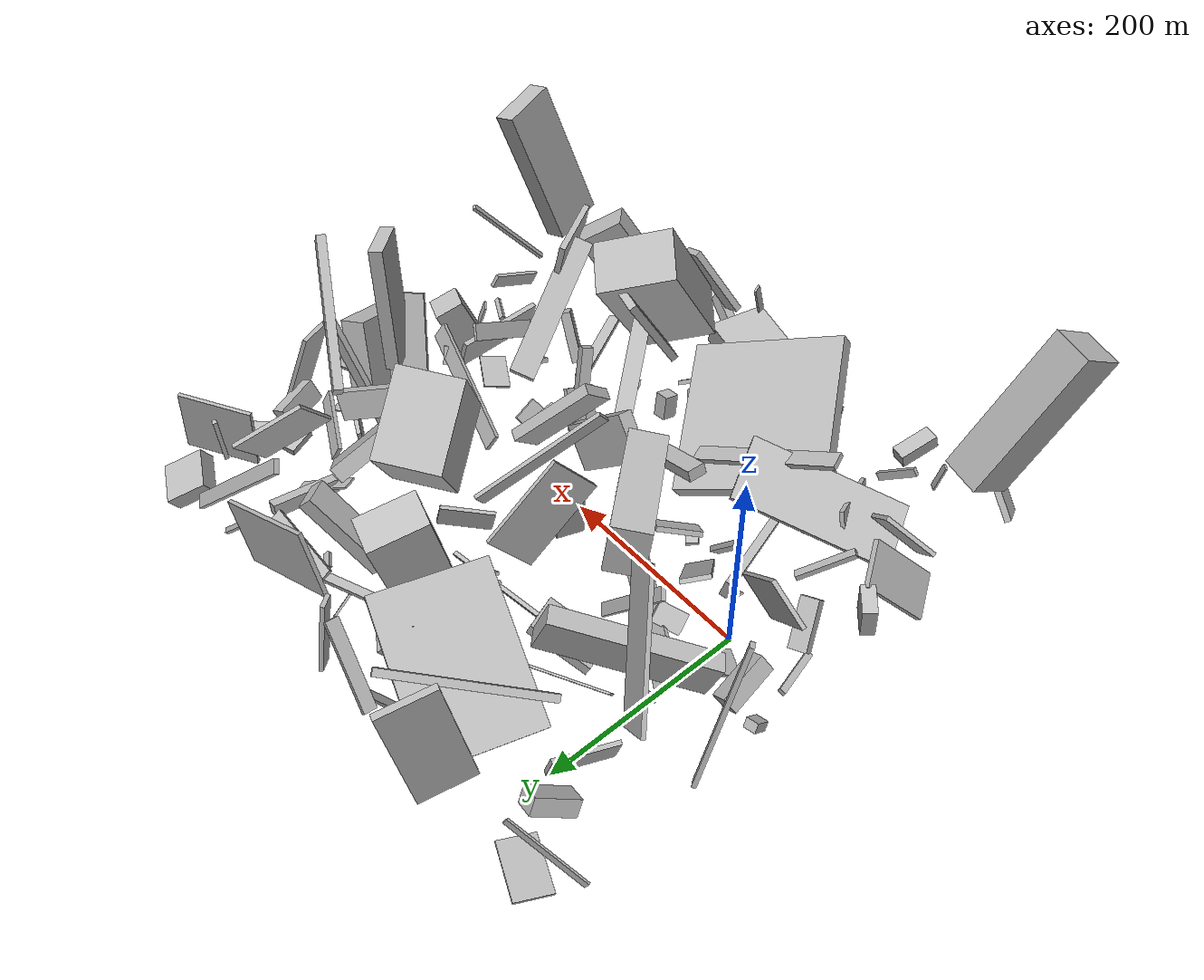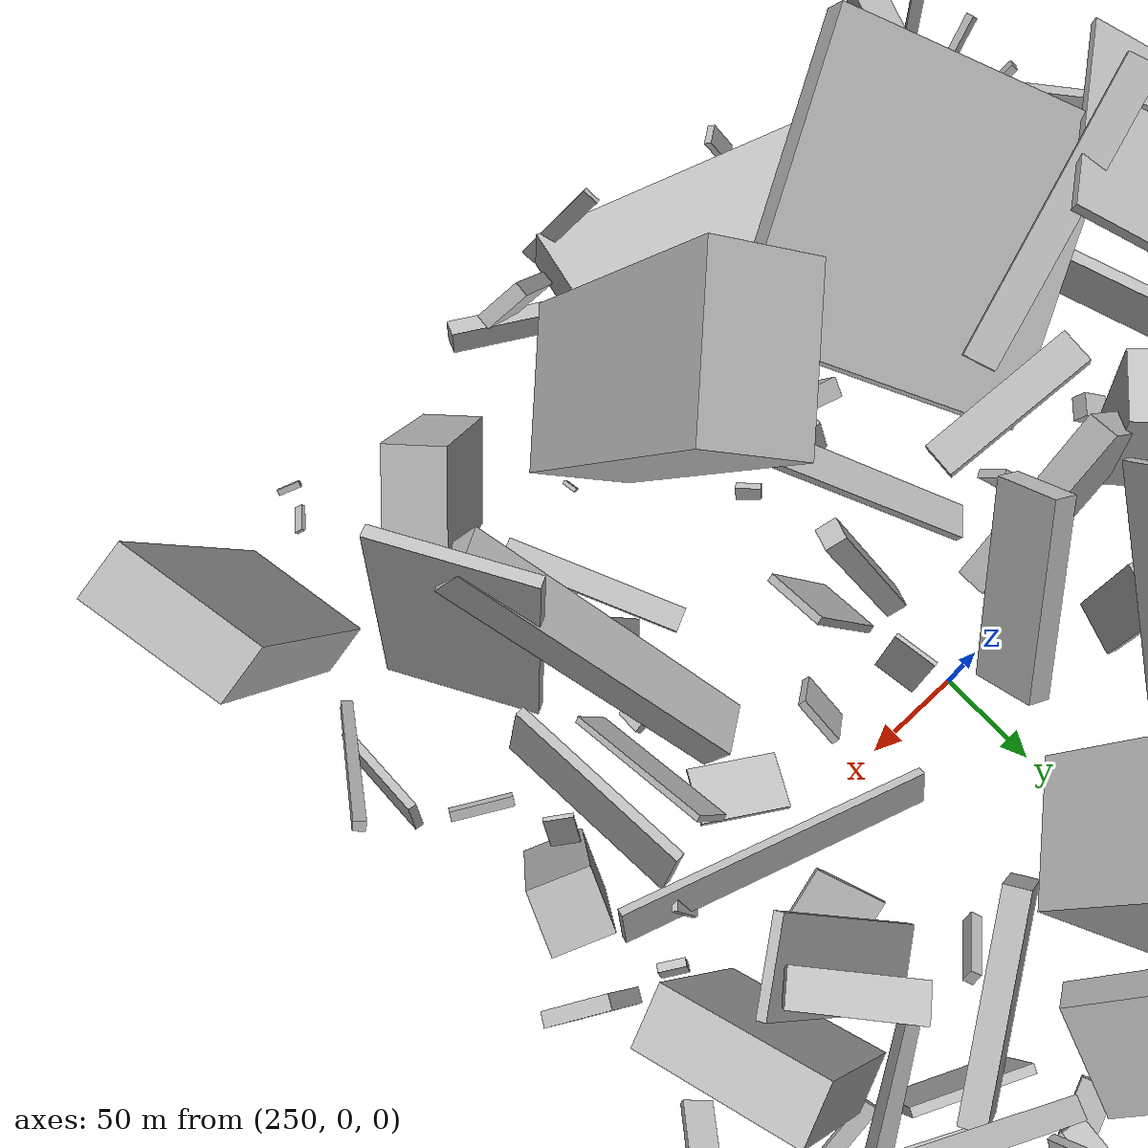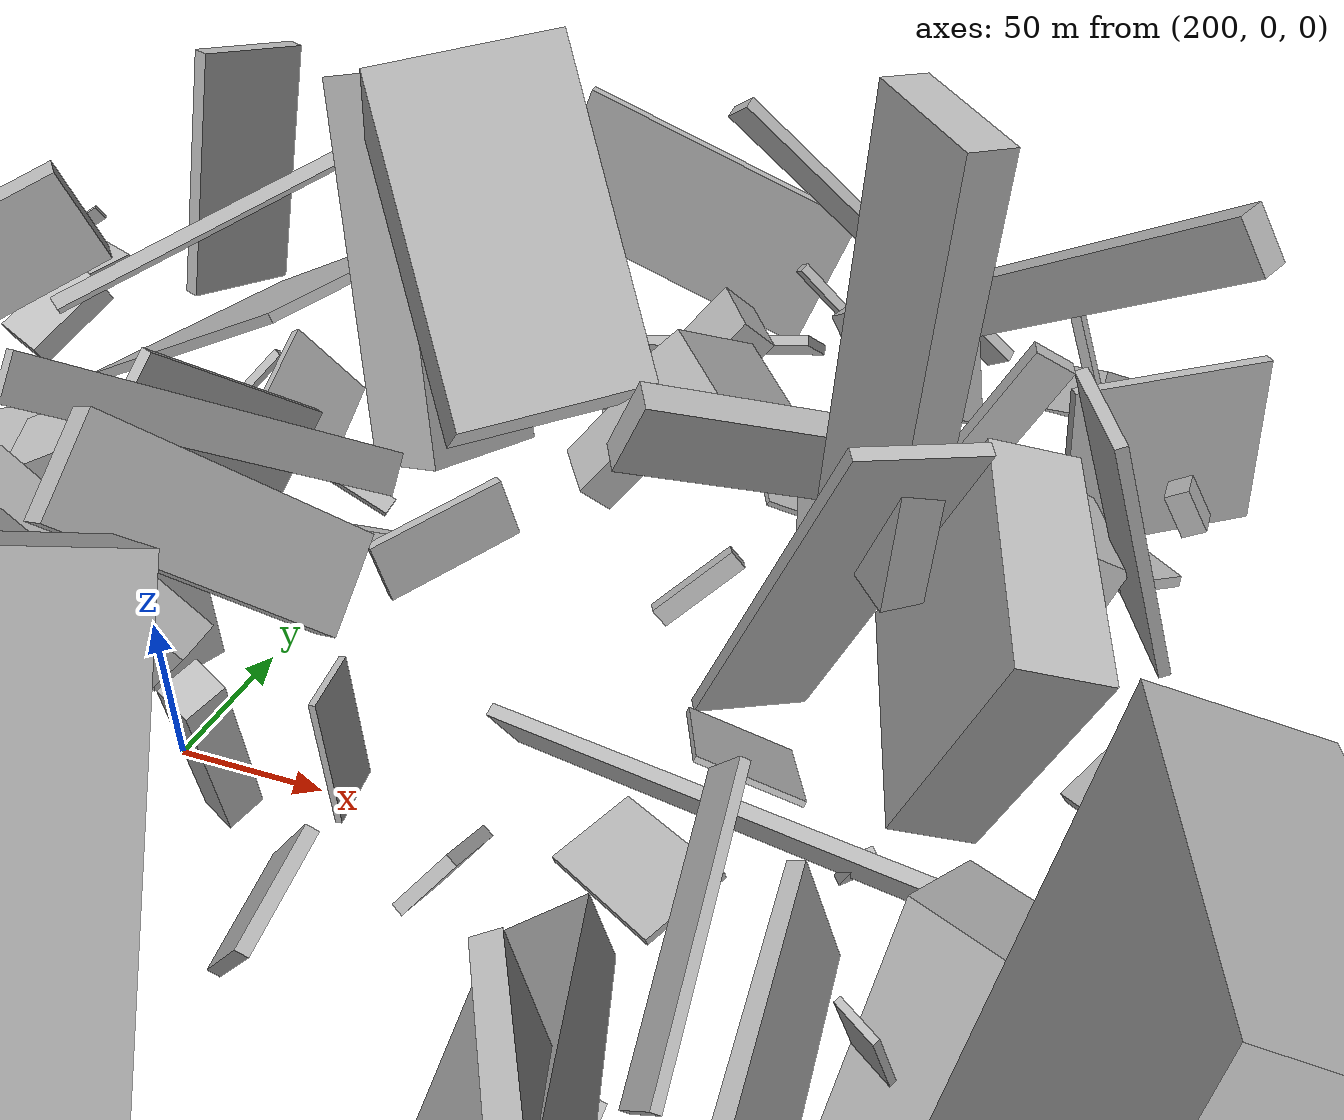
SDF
<sdf version="1.6">
 <world name="default">
  <scene>
   <sky><clouds><speed>12</speed></clouds></sky>
   <ambient>0.4 0.4 0.4 1</ambient>
   <background>0.7 0.7 0.7 1</background>
   <shadows>1</shadows>
  </scene>
  <gravity>0 0 -9.8066</gravity>
  <magnetic_field>6e-06 2.3e-05 -4.2e-05</magnetic_field>
  <physics default="0" name="default_physics" type="ode">
   <ode>
    <solver>
     <type>quick</type>
     <iters>10</iters>
     <sor>1.0</sor>
     <use_dynamic_moi_rescaling>0</use_dynamic_moi_rescaling>
    </solver>
    <constraints>
     <cfm>0</cfm>
     <erp>0.2</erp>
     <contact_max_correcting_vel>100</contact_max_correcting_vel>
     <contact_surface_layer>0.001</contact_surface_layer>
    </constraints>
   </ode>
   <max_step_size>0.004</max_step_size>
   <real_time_factor>1</real_time_factor>
   <real_time_update_rate>250</real_time_update_rate>
  </physics>
  <light name="sun" type="directional">
   <pose>0 0 10 0 0 0</pose>
   <diffuse>0.8 0.8 0.8 1</diffuse>
   <specular>0.2 0.2 0.2 1</specular>
   <attenuation>
    <range>1000</range>
    <constant>0.9</constant>
    <linear>0.01</linear>
    <quadratic>0.001</quadratic>
   </attenuation>
   <direction>-0.5 0.1 -0.9</direction>
  </light>
  <model name="building_1">
   <static>0</static>
   <pose>24.793096692498303 168.19581139344137 49.5074049296235 1.1312948946642172 -0.8036517229261205 2.786725473333905</pose>
   <link name="link">
    <gravity>0</gravity>
    <pose>0 0 75.0 0 0 0</pose>
    <collision name="collision"><geometry><box><size>6 7 150</size></box></geometry></collision>
    <visual name="visual">
     <cast_shadows>0</cast_shadows>
     <geometry><box><size>6 7 150</size></box></geometry>
     <material>
      <script>
       <uri>model://HANNAS_wall/materials/scripts</uri>
       <uri>model://HANNAS_wall/materials/textures</uri>
       <name>vrc/HANNAS_wall</name>
      </script>
     </material>
    </visual>
   </link>
  </model>
  <model name="building_2">
   <static>0</static>
   <pose>168.8053396713834 -48.62277285303505 24.26431392203352 1.2881864655221158 0.8591324916611116 -1.2367148399571342</pose>
   <link name="link">
    <gravity>0</gravity>
    <pose>0 0 2.0 0 0 0</pose>
    <collision name="collision"><geometry><box><size>16 19 4</size></box></geometry></collision>
    <visual name="visual">
     <cast_shadows>0</cast_shadows>
     <geometry><box><size>16 19 4</size></box></geometry>
     <material>
      <script>
       <uri>model://HANNAS_wall/materials/scripts</uri>
       <uri>model://HANNAS_wall/materials/textures</uri>
       <name>vrc/HANNAS_wall</name>
      </script>
     </material>
    </visual>
   </link>
  </model>
  <model name="building_3">
   <static>0</static>
   <pose>-59.367864720709136 -232.25239375942581 92.4109905532498 0.5306030439082318 -0.10531091900524221 -0.18735043741369478</pose>
   <link name="link">
    <gravity>0</gravity>
    <pose>0 0 75.0 0 0 0</pose>
    <collision name="collision"><geometry><box><size>38 52 150</size></box></geometry></collision>
    <visual name="visual">
     <cast_shadows>0</cast_shadows>
     <geometry><box><size>38 52 150</size></box></geometry>
     <material>
      <script>
       <uri>model://HANNAS_wall/materials/scripts</uri>
       <uri>model://HANNAS_wall/materials/textures</uri>
       <name>vrc/HANNAS_wall</name>
      </script>
     </material>
    </visual>
   </link>
  </model>
  <model name="building_4">
   <static>0</static>
   <pose>263.03647146409895 267.4851656963861 57.26977216846049 -0.03833272961277881 -0.39605690153455275 -3.039207817612073</pose>
   <link name="link">
    <gravity>0</gravity>
    <pose>0 0 31.0 0 0 0</pose>
    <collision name="collision"><geometry><box><size>118 4 62</size></box></geometry></collision>
    <visual name="visual">
     <cast_shadows>0</cast_shadows>
     <geometry><box><size>118 4 62</size></box></geometry>
     <material>
      <script>
       <uri>model://HANNAS_wall/materials/scripts</uri>
       <uri>model://HANNAS_wall/materials/textures</uri>
       <name>vrc/HANNAS_wall</name>
      </script>
     </material>
    </visual>
   </link>
  </model>
  <model name="building_5">
   <static>0</static>
   <pose>285.85517207320754 95.06774827823605 86.93801690492187 0.13493003121150643 -0.5815157832856201 -0.9897055192580434</pose>
   <link name="link">
    <gravity>0</gravity>
    <pose>0 0 54.0 0 0 0</pose>
    <collision name="collision"><geometry><box><size>83 61 108</size></box></geometry></collision>
    <visual name="visual">
     <cast_shadows>0</cast_shadows>
     <geometry><box><size>83 61 108</size></box></geometry>
     <material>
      <script>
       <uri>model://HANNAS_wall/materials/scripts</uri>
       <uri>model://HANNAS_wall/materials/textures</uri>
       <name>vrc/HANNAS_wall</name>
      </script>
     </material>
    </visual>
   </link>
  </model>
  <model name="building_6">
   <static>0</static>
   <pose>259.6509988702813 -145.3770697264033 90.13682380349344 1.0791229489966476 -1.0057302092147538 1.8290417907141316</pose>
   <link name="link">
    <gravity>0</gravity>
    <pose>0 0 11.5 0 0 0</pose>
    <collision name="collision"><geometry><box><size>150 8 23</size></box></geometry></collision>
    <visual name="visual">
     <cast_shadows>0</cast_shadows>
     <geometry><box><size>150 8 23</size></box></geometry>
     <material>
      <script>
       <uri>model://HANNAS_wall/materials/scripts</uri>
       <uri>model://HANNAS_wall/materials/textures</uri>
       <name>vrc/HANNAS_wall</name>
      </script>
     </material>
    </visual>
   </link>
  </model>
  <model name="building_7">
   <static>0</static>
   <pose>124.69951320487586 -160.69138520778654 67.32807591150723 0.41972504675591227 -0.38616532295552297 -2.643007711229868</pose>
   <link name="link">
    <gravity>0</gravity>
    <pose>0 0 8.0 0 0 0</pose>
    <collision name="collision"><geometry><box><size>150 150 16</size></box></geometry></collision>
    <visual name="visual">
     <cast_shadows>0</cast_shadows>
     <geometry><box><size>150 150 16</size></box></geometry>
     <material>
      <script>
       <uri>model://HANNAS_wall/materials/scripts</uri>
       <uri>model://HANNAS_wall/materials/textures</uri>
       <name>vrc/HANNAS_wall</name>
      </script>
     </material>
    </visual>
   </link>
  </model>
  <model name="building_8">
   <static>0</static>
   <pose>204.80048753554155 -47.702159353812945 38.16444684129837 0.2839961623136981 1.0717549493889884 -0.6077870350495469</pose>
   <link name="link">
    <gravity>0</gravity>
    <pose>0 0 67.0 0 0 0</pose>
    <collision name="collision"><geometry><box><size>4 17 134</size></box></geometry></collision>
    <visual name="visual">
     <cast_shadows>0</cast_shadows>
     <geometry><box><size>4 17 134</size></box></geometry>
     <material>
      <script>
       <uri>model://HANNAS_wall/materials/scripts</uri>
       <uri>model://HANNAS_wall/materials/textures</uri>
       <name>vrc/HANNAS_wall</name>
      </script>
     </material>
    </visual>
   </link>
  </model>
  <model name="building_9">
   <static>0</static>
   <pose>459.2415905901739 -205.80912013653574 83.49658140967347 -0.2591631520216959 -0.18155681987009847 -1.3571641096785254</pose>
   <link name="link">
    <gravity>0</gravity>
    <pose>0 0 75.0 0 0 0</pose>
    <collision name="collision"><geometry><box><size>55 22 150</size></box></geometry></collision>
    <visual name="visual">
     <cast_shadows>0</cast_shadows>
     <geometry><box><size>55 22 150</size></box></geometry>
     <material>
      <script>
       <uri>model://HANNAS_wall/materials/scripts</uri>
       <uri>model://HANNAS_wall/materials/textures</uri>
       <name>vrc/HANNAS_wall</name>
      </script>
     </material>
    </visual>
   </link>
  </model>
  <model name="building_10">
   <static>0</static>
   <pose>-47.68959779084474 154.3647860653389 73.10178761752809 -0.33368092463802806 -0.7245051040565622 2.835484990418137</pose>
   <link name="link">
    <gravity>0</gravity>
    <pose>0 0 65.5 0 0 0</pose>
    <collision name="collision"><geometry><box><size>43 4 131</size></box></geometry></collision>
    <visual name="visual">
     <cast_shadows>0</cast_shadows>
     <geometry><box><size>43 4 131</size></box></geometry>
     <material>
      <script>
       <uri>model://HANNAS_wall/materials/scripts</uri>
       <uri>model://HANNAS_wall/materials/textures</uri>
       <name>vrc/HANNAS_wall</name>
      </script>
     </material>
    </visual>
   </link>
  </model>
  <model name="building_11">
   <static>0</static>
   <pose>38.94238117270541 254.09804892316535 76.96646925720617 1.7350891535008843 -0.11104195794203885 2.8328328251791577</pose>
   <link name="link">
    <gravity>0</gravity>
    <pose>0 0 26.5 0 0 0</pose>
    <collision name="collision"><geometry><box><size>7 114 53</size></box></geometry></collision>
    <visual name="visual">
     <cast_shadows>0</cast_shadows>
     <geometry><box><size>7 114 53</size></box></geometry>
     <material>
      <script>
       <uri>model://HANNAS_wall/materials/scripts</uri>
       <uri>model://HANNAS_wall/materials/textures</uri>
       <name>vrc/HANNAS_wall</name>
      </script>
     </material>
    </visual>
   </link>
  </model>
  <model name="building_12">
   <static>0</static>
   <pose>92.06836739142696 4.750236727504768 100.409990952442 -0.7303589296694571 -1.402763171710577 -1.6966336196243017</pose>
   <link name="link">
    <gravity>0</gravity>
    <pose>0 0 18.0 0 0 0</pose>
    <collision name="collision"><geometry><box><size>51 125 36</size></box></geometry></collision>
    <visual name="visual">
     <cast_shadows>0</cast_shadows>
     <geometry><box><size>51 125 36</size></box></geometry>
     <material>
      <script>
       <uri>model://HANNAS_wall/materials/scripts</uri>
       <uri>model://HANNAS_wall/materials/textures</uri>
       <name>vrc/HANNAS_wall</name>
      </script>
     </material>
    </visual>
   </link>
  </model>
  <model name="building_13">
   <static>0</static>
   <pose>267.6605799473157 -130.94874827357373 30.96846386329397 1.2072147905298733 -1.082710756713276 -2.083079398568813</pose>
   <link name="link">
    <gravity>0</gravity>
    <pose>0 0 6.0 0 0 0</pose>
    <collision name="collision"><geometry><box><size>7 4 12</size></box></geometry></collision>
    <visual name="visual">
     <cast_shadows>0</cast_shadows>
     <geometry><box><size>7 4 12</size></box></geometry>
     <material>
      <script>
       <uri>model://HANNAS_wall/materials/scripts</uri>
       <uri>model://HANNAS_wall/materials/textures</uri>
       <name>vrc/HANNAS_wall</name>
      </script>
     </material>
    </visual>
   </link>
  </model>
  <model name="building_14">
   <static>0</static>
   <pose>107.75886185038104 208.34520341155167 46.10967357507414 0.040087765200739 -0.47666089245156523 -0.2999473800195148</pose>
   <link name="link">
    <gravity>0</gravity>
    <pose>0 0 2.0 0 0 0</pose>
    <collision name="collision"><geometry><box><size>150 108 4</size></box></geometry></collision>
    <visual name="visual">
     <cast_shadows>0</cast_shadows>
     <geometry><box><size>150 108 4</size></box></geometry>
     <material>
      <script>
       <uri>model://HANNAS_wall/materials/scripts</uri>
       <uri>model://HANNAS_wall/materials/textures</uri>
       <name>vrc/HANNAS_wall</name>
      </script>
     </material>
    </visual>
   </link>
  </model>
  <model name="building_15">
   <static>0</static>
   <pose>263.8235517658701 -62.886654904458396 69.58725831331046 -0.973633495032101 -1.0699772152761018 -0.9388409256764467</pose>
   <link name="link">
    <gravity>0</gravity>
    <pose>0 0 5.5 0 0 0</pose>
    <collision name="collision"><geometry><box><size>80 10 11</size></box></geometry></collision>
    <visual name="visual">
     <cast_shadows>0</cast_shadows>
     <geometry><box><size>80 10 11</size></box></geometry>
     <material>
      <script>
       <uri>model://HANNAS_wall/materials/scripts</uri>
       <uri>model://HANNAS_wall/materials/textures</uri>
       <name>vrc/HANNAS_wall</name>
      </script>
     </material>
    </visual>
   </link>
  </model>
  <model name="building_16">
   <static>0</static>
   <pose>345.2228448444072 -146.4754410458868 12.939576537642377 -0.14851779002124282 -0.08573682832461466 -1.1167403407948364</pose>
   <link name="link">
    <gravity>0</gravity>
    <pose>0 0 2.0 0 0 0</pose>
    <collision name="collision"><geometry><box><size>90 12 4</size></box></geometry></collision>
    <visual name="visual">
     <cast_shadows>0</cast_shadows>
     <geometry><box><size>90 12 4</size></box></geometry>
     <material>
      <script>
       <uri>model://HANNAS_wall/materials/scripts</uri>
       <uri>model://HANNAS_wall/materials/textures</uri>
       <name>vrc/HANNAS_wall</name>
      </script>
     </material>
    </visual>
   </link>
  </model>
  <model name="building_17">
   <static>0</static>
   <pose>-55.43925519525918 -143.04767132898246 76.77545361847622 0.8255333455265249 0.7698998162747802 -0.45425481077730295</pose>
   <link name="link">
    <gravity>0</gravity>
    <pose>0 0 2.0 0 0 0</pose>
    <collision name="collision"><geometry><box><size>35 53 4</size></box></geometry></collision>
    <visual name="visual">
     <cast_shadows>0</cast_shadows>
     <geometry><box><size>35 53 4</size></box></geometry>
     <material>
      <script>
       <uri>model://HANNAS_wall/materials/scripts</uri>
       <uri>model://HANNAS_wall/materials/textures</uri>
       <name>vrc/HANNAS_wall</name>
      </script>
     </material>
    </visual>
   </link>
  </model>
  <model name="building_18">
   <static>0</static>
   <pose>211.10453171936953 184.67694604028543 89.60581939708521 1.8232575828191566 -0.19318669373226394 -1.87461985738655</pose>
   <link name="link">
    <gravity>0</gravity>
    <pose>0 0 16.5 0 0 0</pose>
    <collision name="collision"><geometry><box><size>55 146 33</size></box></geometry></collision>
    <visual name="visual">
     <cast_shadows>0</cast_shadows>
     <geometry><box><size>55 146 33</size></box></geometry>
     <material>
      <script>
       <uri>model://HANNAS_wall/materials/scripts</uri>
       <uri>model://HANNAS_wall/materials/textures</uri>
       <name>vrc/HANNAS_wall</name>
      </script>
     </material>
    </visual>
   </link>
  </model>
  <model name="building_19">
   <static>0</static>
   <pose>472.00417471059876 69.8538557242104 22.926456738517928 -1.0896798849306657 -1.0267276106663328 -2.7639595700852406</pose>
   <link name="link">
    <gravity>0</gravity>
    <pose>0 0 6.5 0 0 0</pose>
    <collision name="collision"><geometry><box><size>4 32 13</size></box></geometry></collision>
    <visual name="visual">
     <cast_shadows>0</cast_shadows>
     <geometry><box><size>4 32 13</size></box></geometry>
     <material>
      <script>
       <uri>model://HANNAS_wall/materials/scripts</uri>
       <uri>model://HANNAS_wall/materials/textures</uri>
       <name>vrc/HANNAS_wall</name>
      </script>
     </material>
    </visual>
   </link>
  </model>
  <model name="building_20">
   <static>0</static>
   <pose>365.0307740110446 -116.42028238443862 65.30680607868318 1.0437830311087748 -0.8741898894755495 2.5886956512332677</pose>
   <link name="link">
    <gravity>0</gravity>
    <pose>0 0 13.0 0 0 0</pose>
    <collision name="collision"><geometry><box><size>17 150 26</size></box></geometry></collision>
    <visual name="visual">
     <cast_shadows>0</cast_shadows>
     <geometry><box><size>17 150 26</size></box></geometry>
     <material>
      <script>
       <uri>model://HANNAS_wall/materials/scripts</uri>
       <uri>model://HANNAS_wall/materials/textures</uri>
       <name>vrc/HANNAS_wall</name>
      </script>
     </material>
    </visual>
   </link>
  </model>
  <model name="building_21">
   <static>0</static>
   <pose>194.08084231534218 -212.58871243280262 31.631690254402187 1.581392650125628 -0.10717220341301056 -0.215393158977691</pose>
   <link name="link">
    <gravity>0</gravity>
    <pose>0 0 30.5 0 0 0</pose>
    <collision name="collision"><geometry><box><size>150 24 61</size></box></geometry></collision>
    <visual name="visual">
     <cast_shadows>0</cast_shadows>
     <geometry><box><size>150 24 61</size></box></geometry>
     <material>
      <script>
       <uri>model://HANNAS_wall/materials/scripts</uri>
       <uri>model://HANNAS_wall/materials/textures</uri>
       <name>vrc/HANNAS_wall</name>
      </script>
     </material>
    </visual>
   </link>
  </model>
  <model name="building_22">
   <static>0</static>
   <pose>455.39509880448725 -36.48258940865607 64.58165439071153 2.762808254975373 0.05219522985441237 -0.37821665882999467</pose>
   <link name="link">
    <gravity>0</gravity>
    <pose>0 0 31.5 0 0 0</pose>
    <collision name="collision"><geometry><box><size>28 30 63</size></box></geometry></collision>
    <visual name="visual">
     <cast_shadows>0</cast_shadows>
     <geometry><box><size>28 30 63</size></box></geometry>
     <material>
      <script>
       <uri>model://HANNAS_wall/materials/scripts</uri>
       <uri>model://HANNAS_wall/materials/textures</uri>
       <name>vrc/HANNAS_wall</name>
      </script>
     </material>
    </visual>
   </link>
  </model>
  <model name="building_23">
   <static>0</static>
   <pose>-28.73925012321936 -12.545407277168431 73.49264742716169 -1.1589664787374676 -0.8212757556505275 2.659889083329974</pose>
   <link name="link">
    <gravity>0</gravity>
    <pose>0 0 2.0 0 0 0</pose>
    <collision name="collision"><geometry><box><size>91 46 4</size></box></geometry></collision>
    <visual name="visual">
     <cast_shadows>0</cast_shadows>
     <geometry><box><size>91 46 4</size></box></geometry>
     <material>
      <script>
       <uri>model://HANNAS_wall/materials/scripts</uri>
       <uri>model://HANNAS_wall/materials/textures</uri>
       <name>vrc/HANNAS_wall</name>
      </script>
     </material>
    </visual>
   </link>
  </model>
  <model name="building_24">
   <static>0</static>
   <pose>14.591894694779839 -180.31315361042851 42.802350549079534 1.2302763048712029 -0.2673526523090715 -2.6469734096374937</pose>
   <link name="link">
    <gravity>0</gravity>
    <pose>0 0 35.0 0 0 0</pose>
    <collision name="collision"><geometry><box><size>4 33 70</size></box></geometry></collision>
    <visual name="visual">
     <cast_shadows>0</cast_shadows>
     <geometry><box><size>4 33 70</size></box></geometry>
     <material>
      <script>
       <uri>model://HANNAS_wall/materials/scripts</uri>
       <uri>model://HANNAS_wall/materials/textures</uri>
       <name>vrc/HANNAS_wall</name>
      </script>
     </material>
    </visual>
   </link>
  </model>
  <model name="building_25">
   <static>0</static>
   <pose>373.0119426935905 138.91956415236365 111.66071159586862 -0.27823387893055074 -1.0244783643637487 2.9327266899046176</pose>
   <link name="link">
    <gravity>0</gravity>
    <pose>0 0 75.0 0 0 0</pose>
    <collision name="collision"><geometry><box><size>16 9 150</size></box></geometry></collision>
    <visual name="visual">
     <cast_shadows>0</cast_shadows>
     <geometry><box><size>16 9 150</size></box></geometry>
     <material>
      <script>
       <uri>model://HANNAS_wall/materials/scripts</uri>
       <uri>model://HANNAS_wall/materials/textures</uri>
       <name>vrc/HANNAS_wall</name>
      </script>
     </material>
    </visual>
   </link>
  </model>
  <model name="building_26">
   <static>0</static>
   <pose>-70.31714376284003 -124.39760215544086 47.37824749308297 0.9161456227548778 -0.4019110181256023 -1.0033505730773933</pose>
   <link name="link">
    <gravity>0</gravity>
    <pose>0 0 2.5 0 0 0</pose>
    <collision name="collision"><geometry><box><size>43 81 5</size></box></geometry></collision>
    <visual name="visual">
     <cast_shadows>0</cast_shadows>
     <geometry><box><size>43 81 5</size></box></geometry>
     <material>
      <script>
       <uri>model://HANNAS_wall/materials/scripts</uri>
       <uri>model://HANNAS_wall/materials/textures</uri>
       <name>vrc/HANNAS_wall</name>
      </script>
     </material>
    </visual>
   </link>
  </model>
  <model name="building_27">
   <static>0</static>
   <pose>196.71632096892884 272.50762240012443 60.34691920871367 0.5320310369063643 -1.355222844628276 -1.3935005106016631</pose>
   <link name="link">
    <gravity>0</gravity>
    <pose>0 0 8.0 0 0 0</pose>
    <collision name="collision"><geometry><box><size>73 4 16</size></box></geometry></collision>
    <visual name="visual">
     <cast_shadows>0</cast_shadows>
     <geometry><box><size>73 4 16</size></box></geometry>
     <material>
      <script>
       <uri>model://HANNAS_wall/materials/scripts</uri>
       <uri>model://HANNAS_wall/materials/textures</uri>
       <name>vrc/HANNAS_wall</name>
      </script>
     </material>
    </visual>
   </link>
  </model>
  <model name="building_28">
   <static>0</static>
   <pose>412.4956900947473 -69.24407321633116 29.606353960664467 0.1931557898543584 1.2766564398999496 0.26510275548974493</pose>
   <link name="link">
    <gravity>0</gravity>
    <pose>0 0 2.5 0 0 0</pose>
    <collision name="collision"><geometry><box><size>35 95 5</size></box></geometry></collision>
    <visual name="visual">
     <cast_shadows>0</cast_shadows>
     <geometry><box><size>35 95 5</size></box></geometry>
     <material>
      <script>
       <uri>model://HANNAS_wall/materials/scripts</uri>
       <uri>model://HANNAS_wall/materials/textures</uri>
       <name>vrc/HANNAS_wall</name>
      </script>
     </material>
    </visual>
   </link>
  </model>
  <model name="building_29">
   <static>0</static>
   <pose>310.00653551047003 -142.08531714202906 108.00430819249836 1.2336522797450264 -0.4701383384215075 -0.647386164182315</pose>
   <link name="link">
    <gravity>0</gravity>
    <pose>0 0 38.5 0 0 0</pose>
    <collision name="collision"><geometry><box><size>51 150 77</size></box></geometry></collision>
    <visual name="visual">
     <cast_shadows>0</cast_shadows>
     <geometry><box><size>51 150 77</size></box></geometry>
     <material>
      <script>
       <uri>model://HANNAS_wall/materials/scripts</uri>
       <uri>model://HANNAS_wall/materials/textures</uri>
       <name>vrc/HANNAS_wall</name>
      </script>
     </material>
    </visual>
   </link>
  </model>
  <model name="building_30">
   <static>0</static>
   <pose>351.01289641679364 266.13602024073055 46.52521317034503 -2.4450187673026265 -0.8097752759222964 -2.927714700753296</pose>
   <link name="link">
    <gravity>0</gravity>
    <pose>0 0 2.0 0 0 0</pose>
    <collision name="collision"><geometry><box><size>82 5 4</size></box></geometry></collision>
    <visual name="visual">
     <cast_shadows>0</cast_shadows>
     <geometry><box><size>82 5 4</size></box></geometry>
     <material>
      <script>
       <uri>model://HANNAS_wall/materials/scripts</uri>
       <uri>model://HANNAS_wall/materials/textures</uri>
       <name>vrc/HANNAS_wall</name>
      </script>
     </material>
    </visual>
   </link>
  </model>
  <model name="building_31">
   <static>0</static>
   <pose>164.8208078475925 162.1392026932743 23.44454339594291 -0.5910642076057109 -0.30495924785667283 1.737402867334596</pose>
   <link name="link">
    <gravity>0</gravity>
    <pose>0 0 18.5 0 0 0</pose>
    <collision name="collision"><geometry><box><size>39 4 37</size></box></geometry></collision>
    <visual name="visual">
     <cast_shadows>0</cast_shadows>
     <geometry><box><size>39 4 37</size></box></geometry>
     <material>
      <script>
       <uri>model://HANNAS_wall/materials/scripts</uri>
       <uri>model://HANNAS_wall/materials/textures</uri>
       <name>vrc/HANNAS_wall</name>
      </script>
     </material>
    </visual>
   </link>
  </model>
  <model name="building_32">
   <static>0</static>
   <pose>447.25743173991134 59.5828461271806 63.03762369217427 0.8699033775675232 -1.1600909487752653 -0.5154917881440723</pose>
   <link name="link">
    <gravity>0</gravity>
    <pose>0 0 13.5 0 0 0</pose>
    <collision name="collision"><geometry><box><size>86 73 27</size></box></geometry></collision>
    <visual name="visual">
     <cast_shadows>0</cast_shadows>
     <geometry><box><size>86 73 27</size></box></geometry>
     <material>
      <script>
       <uri>model://HANNAS_wall/materials/scripts</uri>
       <uri>model://HANNAS_wall/materials/textures</uri>
       <name>vrc/HANNAS_wall</name>
      </script>
     </material>
    </visual>
   </link>
  </model>
  <model name="building_33">
   <static>0</static>
   <pose>290.1351687367234 236.48648257057675 13.083177044019566 1.4321704329737104 0.003907793590486828 -1.2718227332262604</pose>
   <link name="link">
    <gravity>0</gravity>
    <pose>0 0 66.0 0 0 0</pose>
    <collision name="collision"><geometry><box><size>9 4 132</size></box></geometry></collision>
    <visual name="visual">
     <cast_shadows>0</cast_shadows>
     <geometry><box><size>9 4 132</size></box></geometry>
     <material>
      <script>
       <uri>model://HANNAS_wall/materials/scripts</uri>
       <uri>model://HANNAS_wall/materials/textures</uri>
       <name>vrc/HANNAS_wall</name>
      </script>
     </material>
    </visual>
   </link>
  </model>
  <model name="building_34">
   <static>0</static>
   <pose>444.17196289707096 228.60955305083277 54.83331223394984 1.6094641841759407 0.3900204075560647 2.865676450977857</pose>
   <link name="link">
    <gravity>0</gravity>
    <pose>0 0 2.0 0 0 0</pose>
    <collision name="collision"><geometry><box><size>4 88 4</size></box></geometry></collision>
    <visual name="visual">
     <cast_shadows>0</cast_shadows>
     <geometry><box><size>4 88 4</size></box></geometry>
     <material>
      <script>
       <uri>model://HANNAS_wall/materials/scripts</uri>
       <uri>model://HANNAS_wall/materials/textures</uri>
       <name>vrc/HANNAS_wall</name>
      </script>
     </material>
    </visual>
   </link>
  </model>
  <model name="building_35">
   <static>0</static>
   <pose>362.4978224439738 -221.44047607727177 51.540805088940715 -0.05079563446337559 -0.582685306028434 -2.3550856350923937</pose>
   <link name="link">
    <gravity>0</gravity>
    <pose>0 0 40.0 0 0 0</pose>
    <collision name="collision"><geometry><box><size>50 27 80</size></box></geometry></collision>
    <visual name="visual">
     <cast_shadows>0</cast_shadows>
     <geometry><box><size>50 27 80</size></box></geometry>
     <material>
      <script>
       <uri>model://HANNAS_wall/materials/scripts</uri>
       <uri>model://HANNAS_wall/materials/textures</uri>
       <name>vrc/HANNAS_wall</name>
      </script>
     </material>
    </visual>
   </link>
  </model>
  <model name="building_36">
   <static>0</static>
   <pose>440.44851173203875 199.91031694396088 38.90976830088263 1.5041174146947904 -0.01043804281663071 2.134613622329355</pose>
   <link name="link">
    <gravity>0</gravity>
    <pose>0 0 37.0 0 0 0</pose>
    <collision name="collision"><geometry><box><size>4 67 74</size></box></geometry></collision>
    <visual name="visual">
     <cast_shadows>0</cast_shadows>
     <geometry><box><size>4 67 74</size></box></geometry>
     <material>
      <script>
       <uri>model://HANNAS_wall/materials/scripts</uri>
       <uri>model://HANNAS_wall/materials/textures</uri>
       <name>vrc/HANNAS_wall</name>
      </script>
     </material>
    </visual>
   </link>
  </model>
  <model name="building_37">
   <static>0</static>
   <pose>137.51583433232963 181.42498766872015 25.23800191470125 -3.1019133106257493 -0.30303813223686765 0.7534132209978549</pose>
   <link name="link">
    <gravity>0</gravity>
    <pose>0 0 5.5 0 0 0</pose>
    <collision name="collision"><geometry><box><size>4 6 11</size></box></geometry></collision>
    <visual name="visual">
     <cast_shadows>0</cast_shadows>
     <geometry><box><size>4 6 11</size></box></geometry>
     <material>
      <script>
       <uri>model://HANNAS_wall/materials/scripts</uri>
       <uri>model://HANNAS_wall/materials/textures</uri>
       <name>vrc/HANNAS_wall</name>
      </script>
     </material>
    </visual>
   </link>
  </model>
  <model name="building_38">
   <static>0</static>
   <pose>-81.85622585892777 -79.85902239275019 35.48707502694896 1.265372610476518 0.11262050423304477 0.8223140760192229</pose>
   <link name="link">
    <gravity>0</gravity>
    <pose>0 0 12.5 0 0 0</pose>
    <collision name="collision"><geometry><box><size>13 58 25</size></box></geometry></collision>
    <visual name="visual">
     <cast_shadows>0</cast_shadows>
     <geometry><box><size>13 58 25</size></box></geometry>
     <material>
      <script>
       <uri>model://HANNAS_wall/materials/scripts</uri>
       <uri>model://HANNAS_wall/materials/textures</uri>
       <name>vrc/HANNAS_wall</name>
      </script>
     </material>
    </visual>
   </link>
  </model>
  <model name="building_39">
   <static>0</static>
   <pose>-43.62467939067638 268.54843054093453 7.390177772720591 -1.0149583974153422 1.3557874893878272 1.8964086453849316</pose>
   <link name="link">
    <gravity>0</gravity>
    <pose>0 0 3.0 0 0 0</pose>
    <collision name="collision"><geometry><box><size>4 22 6</size></box></geometry></collision>
    <visual name="visual">
     <cast_shadows>0</cast_shadows>
     <geometry><box><size>4 22 6</size></box></geometry>
     <material>
      <script>
       <uri>model://HANNAS_wall/materials/scripts</uri>
       <uri>model://HANNAS_wall/materials/textures</uri>
       <name>vrc/HANNAS_wall</name>
      </script>
     </material>
    </visual>
   </link>
  </model>
  <model name="building_40">
   <static>0</static>
   <pose>254.59395941677184 20.80287378241911 64.93861815000187 0.4854140651303474 0.7124354289118852 -1.6222809068791284</pose>
   <link name="link">
    <gravity>0</gravity>
    <pose>0 0 45.5 0 0 0</pose>
    <collision name="collision"><geometry><box><size>32 11 91</size></box></geometry></collision>
    <visual name="visual">
     <cast_shadows>0</cast_shadows>
     <geometry><box><size>32 11 91</size></box></geometry>
     <material>
      <script>
       <uri>model://HANNAS_wall/materials/scripts</uri>
       <uri>model://HANNAS_wall/materials/textures</uri>
       <name>vrc/HANNAS_wall</name>
      </script>
     </material>
    </visual>
   </link>
  </model>
  <model name="building_41">
   <static>0</static>
   <pose>438.4606175346938 9.059758295500464 11.6268596929024 -1.8203518254372582 -0.14092574829041224 2.60640521400767</pose>
   <link name="link">
    <gravity>0</gravity>
    <pose>0 0 2.0 0 0 0</pose>
    <collision name="collision"><geometry><box><size>13 10 4</size></box></geometry></collision>
    <visual name="visual">
     <cast_shadows>0</cast_shadows>
     <geometry><box><size>13 10 4</size></box></geometry>
     <material>
      <script>
       <uri>model://HANNAS_wall/materials/scripts</uri>
       <uri>model://HANNAS_wall/materials/textures</uri>
       <name>vrc/HANNAS_wall</name>
      </script>
     </material>
    </visual>
   </link>
  </model>
  <model name="building_42">
   <static>0</static>
   <pose>2.5605970607238735 -91.43303330353929 67.61811676619784 1.274605108122901 -0.31032448423551406 0.5585483696015138</pose>
   <link name="link">
    <gravity>0</gravity>
    <pose>0 0 32.0 0 0 0</pose>
    <collision name="collision"><geometry><box><size>150 4 64</size></box></geometry></collision>
    <visual name="visual">
     <cast_shadows>0</cast_shadows>
     <geometry><box><size>150 4 64</size></box></geometry>
     <material>
      <script>
       <uri>model://HANNAS_wall/materials/scripts</uri>
       <uri>model://HANNAS_wall/materials/textures</uri>
       <name>vrc/HANNAS_wall</name>
      </script>
     </material>
    </visual>
   </link>
  </model>
  <model name="building_43">
   <static>0</static>
   <pose>58.821212411557426 43.354791335235156 19.36550935304233 2.236260912155624 -0.09376503511660356 -0.5264561615918604</pose>
   <link name="link">
    <gravity>0</gravity>
    <pose>0 0 2.0 0 0 0</pose>
    <collision name="collision"><geometry><box><size>150 27 4</size></box></geometry></collision>
    <visual name="visual">
     <cast_shadows>0</cast_shadows>
     <geometry><box><size>150 27 4</size></box></geometry>
     <material>
      <script>
       <uri>model://HANNAS_wall/materials/scripts</uri>
       <uri>model://HANNAS_wall/materials/textures</uri>
       <name>vrc/HANNAS_wall</name>
      </script>
     </material>
    </visual>
   </link>
  </model>
  <model name="building_44">
   <static>0</static>
   <pose>399.6212533064511 223.2782744224587 70.91785444697206 -0.7179844604672067 -0.923344178492602 1.9558265253955083</pose>
   <link name="link">
    <gravity>0</gravity>
    <pose>0 0 36.5 0 0 0</pose>
    <collision name="collision"><geometry><box><size>58 4 73</size></box></geometry></collision>
    <visual name="visual">
     <cast_shadows>0</cast_shadows>
     <geometry><box><size>58 4 73</size></box></geometry>
     <material>
      <script>
       <uri>model://HANNAS_wall/materials/scripts</uri>
       <uri>model://HANNAS_wall/materials/textures</uri>
       <name>vrc/HANNAS_wall</name>
      </script>
     </material>
    </visual>
   </link>
  </model>
  <model name="building_45">
   <static>0</static>
   <pose>27.61211438017165 30.759411747172614 20.669414505358958 1.0094985872402418 -0.8913240492226028 2.534697746085568</pose>
   <link name="link">
    <gravity>0</gravity>
    <pose>0 0 13.5 0 0 0</pose>
    <collision name="collision"><geometry><box><size>15 20 27</size></box></geometry></collision>
    <visual name="visual">
     <cast_shadows>0</cast_shadows>
     <geometry><box><size>15 20 27</size></box></geometry>
     <material>
      <script>
       <uri>model://HANNAS_wall/materials/scripts</uri>
       <uri>model://HANNAS_wall/materials/textures</uri>
       <name>vrc/HANNAS_wall</name>
      </script>
     </material>
    </visual>
   </link>
  </model>
  <model name="building_46">
   <static>0</static>
   <pose>341.77466628804825 140.5615206427859 64.71192747775166 0.9030203522750172 -0.49533664817273704 -1.8058443134780096</pose>
   <link name="link">
    <gravity>0</gravity>
    <pose>0 0 19.0 0 0 0</pose>
    <collision name="collision"><geometry><box><size>54 16 38</size></box></geometry></collision>
    <visual name="visual">
     <cast_shadows>0</cast_shadows>
     <geometry><box><size>54 16 38</size></box></geometry>
     <material>
      <script>
       <uri>model://HANNAS_wall/materials/scripts</uri>
       <uri>model://HANNAS_wall/materials/textures</uri>
       <name>vrc/HANNAS_wall</name>
      </script>
     </material>
    </visual>
   </link>
  </model>
  <model name="building_47">
   <static>0</static>
   <pose>439.06787938644027 166.85211575531372 17.96984781514588 -0.03253739653758626 0.1433754381088489 1.876050689655403</pose>
   <link name="link">
    <gravity>0</gravity>
    <pose>0 0 3.5 0 0 0</pose>
    <collision name="collision"><geometry><box><size>27 35 7</size></box></geometry></collision>
    <visual name="visual">
     <cast_shadows>0</cast_shadows>
     <geometry><box><size>27 35 7</size></box></geometry>
     <material>
      <script>
       <uri>model://HANNAS_wall/materials/scripts</uri>
       <uri>model://HANNAS_wall/materials/textures</uri>
       <name>vrc/HANNAS_wall</name>
      </script>
     </material>
    </visual>
   </link>
  </model>
  <model name="building_48">
   <static>0</static>
   <pose>307.94928239386667 -29.634082417029802 18.953289517317998 2.4929276162944505 -0.7750178104519525 0.5454878994462603</pose>
   <link name="link">
    <gravity>0</gravity>
    <pose>0 0 2.0 0 0 0</pose>
    <collision name="collision"><geometry><box><size>22 25 4</size></box></geometry></collision>
    <visual name="visual">
     <cast_shadows>0</cast_shadows>
     <geometry><box><size>22 25 4</size></box></geometry>
     <material>
      <script>
       <uri>model://HANNAS_wall/materials/scripts</uri>
       <uri>model://HANNAS_wall/materials/textures</uri>
       <name>vrc/HANNAS_wall</name>
      </script>
     </material>
    </visual>
   </link>
  </model>
  <model name="building_49">
   <static>0</static>
   <pose>-87.95251890614003 102.10034816414733 84.03589528166793 1.850242172636725 -0.1944566517270499 0.596191942119423</pose>
   <link name="link">
    <gravity>0</gravity>
    <pose>0 0 4.0 0 0 0</pose>
    <collision name="collision"><geometry><box><size>4 150 8</size></box></geometry></collision>
    <visual name="visual">
     <cast_shadows>0</cast_shadows>
     <geometry><box><size>4 150 8</size></box></geometry>
     <material>
      <script>
       <uri>model://HANNAS_wall/materials/scripts</uri>
       <uri>model://HANNAS_wall/materials/textures</uri>
       <name>vrc/HANNAS_wall</name>
      </script>
     </material>
    </visual>
   </link>
  </model>
  <model name="building_50">
   <static>0</static>
   <pose>364.5477886768533 229.2090518336988 25.94396227206424 1.6446722120407755 0.2002600968755134 -0.08162997838149966</pose>
   <link name="link">
    <gravity>0</gravity>
    <pose>0 0 32.0 0 0 0</pose>
    <collision name="collision"><geometry><box><size>11 13 64</size></box></geometry></collision>
    <visual name="visual">
     <cast_shadows>0</cast_shadows>
     <geometry><box><size>11 13 64</size></box></geometry>
     <material>
      <script>
       <uri>model://HANNAS_wall/materials/scripts</uri>
       <uri>model://HANNAS_wall/materials/textures</uri>
       <name>vrc/HANNAS_wall</name>
      </script>
     </material>
    </visual>
   </link>
  </model>
  <model name="building_51">
   <static>0</static>
   <pose>240.8578716944575 -165.10216349768365 27.941208919265552 -0.9815934243789982 -0.5152455981605337 1.7284640368286868</pose>
   <link name="link">
    <gravity>0</gravity>
    <pose>0 0 35.0 0 0 0</pose>
    <collision name="collision"><geometry><box><size>10 4 70</size></box></geometry></collision>
    <visual name="visual">
     <cast_shadows>0</cast_shadows>
     <geometry><box><size>10 4 70</size></box></geometry>
     <material>
      <script>
       <uri>model://HANNAS_wall/materials/scripts</uri>
       <uri>model://HANNAS_wall/materials/textures</uri>
       <name>vrc/HANNAS_wall</name>
      </script>
     </material>
    </visual>
   </link>
  </model>
  <model name="building_52">
   <static>0</static>
   <pose>347.52881307916164 261.60120713949317 88.8292002017037 0.933617160002334 -0.522816494959689 1.3253689435234117</pose>
   <link name="link">
    <gravity>0</gravity>
    <pose>0 0 6.5 0 0 0</pose>
    <collision name="collision"><geometry><box><size>5 150 13</size></box></geometry></collision>
    <visual name="visual">
     <cast_shadows>0</cast_shadows>
     <geometry><box><size>5 150 13</size></box></geometry>
     <material>
      <script>
       <uri>model://HANNAS_wall/materials/scripts</uri>
       <uri>model://HANNAS_wall/materials/textures</uri>
       <name>vrc/HANNAS_wall</name>
      </script>
     </material>
    </visual>
   </link>
  </model>
  <model name="building_53">
   <static>0</static>
   <pose>228.88411336831416 93.11528386754628 54.94287110256511 0.9512311976258488 -0.19884306001032645 -0.33774789031447416</pose>
   <link name="link">
    <gravity>0</gravity>
    <pose>0 0 69.5 0 0 0</pose>
    <collision name="collision"><geometry><box><size>4 15 139</size></box></geometry></collision>
    <visual name="visual">
     <cast_shadows>0</cast_shadows>
     <geometry><box><size>4 15 139</size></box></geometry>
     <material>
      <script>
       <uri>model://HANNAS_wall/materials/scripts</uri>
       <uri>model://HANNAS_wall/materials/textures</uri>
       <name>vrc/HANNAS_wall</name>
      </script>
     </material>
    </visual>
   </link>
  </model>
  <model name="building_54">
   <static>0</static>
   <pose>296.54625090478214 184.01440281856296 40.30643598195662 -1.427825337167217 -0.8134062605364885 0.5019441139701522</pose>
   <link name="link">
    <gravity>0</gravity>
    <pose>0 0 13.5 0 0 0</pose>
    <collision name="collision"><geometry><box><size>92 16 27</size></box></geometry></collision>
    <visual name="visual">
     <cast_shadows>0</cast_shadows>
     <geometry><box><size>92 16 27</size></box></geometry>
     <material>
      <script>
       <uri>model://HANNAS_wall/materials/scripts</uri>
       <uri>model://HANNAS_wall/materials/textures</uri>
       <name>vrc/HANNAS_wall</name>
      </script>
     </material>
    </visual>
   </link>
  </model>
  <model name="building_55">
   <static>0</static>
   <pose>220.31857396280617 -19.69613214007593 53.81113984320597 0.8156167246883899 0.13692948063860463 -1.6038663871257706</pose>
   <link name="link">
    <gravity>0</gravity>
    <pose>0 0 43.5 0 0 0</pose>
    <collision name="collision"><geometry><box><size>14 45 87</size></box></geometry></collision>
    <visual name="visual">
     <cast_shadows>0</cast_shadows>
     <geometry><box><size>14 45 87</size></box></geometry>
     <material>
      <script>
       <uri>model://HANNAS_wall/materials/scripts</uri>
       <uri>model://HANNAS_wall/materials/textures</uri>
       <name>vrc/HANNAS_wall</name>
      </script>
     </material>
    </visual>
   </link>
  </model>
  <model name="building_56">
   <static>0</static>
   <pose>442.5566771360339 166.95651427035529 41.0105760000384 1.523225140470744 0.4346242677337635 0.3567465093203285</pose>
   <link name="link">
    <gravity>0</gravity>
    <pose>0 0 23.0 0 0 0</pose>
    <collision name="collision"><geometry><box><size>14 22 46</size></box></geometry></collision>
    <visual name="visual">
     <cast_shadows>0</cast_shadows>
     <geometry><box><size>14 22 46</size></box></geometry>
     <material>
      <script>
       <uri>model://HANNAS_wall/materials/scripts</uri>
       <uri>model://HANNAS_wall/materials/textures</uri>
       <name>vrc/HANNAS_wall</name>
      </script>
     </material>
    </visual>
   </link>
  </model>
  <model name="building_57">
   <static>0</static>
   <pose>16.931518370422502 101.62656755926767 75.19001400525893 1.7750623711911302 -1.1989111846395932 -2.5657098491040213</pose>
   <link name="link">
    <gravity>0</gravity>
    <pose>0 0 9.0 0 0 0</pose>
    <collision name="collision"><geometry><box><size>39 150 18</size></box></geometry></collision>
    <visual name="visual">
     <cast_shadows>0</cast_shadows>
     <geometry><box><size>39 150 18</size></box></geometry>
     <material>
      <script>
       <uri>model://HANNAS_wall/materials/scripts</uri>
       <uri>model://HANNAS_wall/materials/textures</uri>
       <name>vrc/HANNAS_wall</name>
      </script>
     </material>
    </visual>
   </link>
  </model>
  <model name="building_58">
   <static>0</static>
   <pose>32.74460744920229 -225.45943803992233 20.267960958363027 -0.9069449466090056 -0.12577745973499055 1.7348109178537219</pose>
   <link name="link">
    <gravity>0</gravity>
    <pose>0 0 21.5 0 0 0</pose>
    <collision name="collision"><geometry><box><size>4 8 43</size></box></geometry></collision>
    <visual name="visual">
     <cast_shadows>0</cast_shadows>
     <geometry><box><size>4 8 43</size></box></geometry>
     <material>
      <script>
       <uri>model://HANNAS_wall/materials/scripts</uri>
       <uri>model://HANNAS_wall/materials/textures</uri>
       <name>vrc/HANNAS_wall</name>
      </script>
     </material>
    </visual>
   </link>
  </model>
  <model name="building_59">
   <static>0</static>
   <pose>-20.411742021939634 25.271290061528187 13.879730376319802 -2.9514600816329692 0.5416412229957582 -1.8872278969736078</pose>
   <link name="link">
    <gravity>0</gravity>
    <pose>0 0 2.0 0 0 0</pose>
    <collision name="collision"><geometry><box><size>21 25 4</size></box></geometry></collision>
    <visual name="visual">
     <cast_shadows>0</cast_shadows>
     <geometry><box><size>21 25 4</size></box></geometry>
     <material>
      <script>
       <uri>model://HANNAS_wall/materials/scripts</uri>
       <uri>model://HANNAS_wall/materials/textures</uri>
       <name>vrc/HANNAS_wall</name>
      </script>
     </material>
    </visual>
   </link>
  </model>
  <model name="building_60">
   <static>0</static>
   <pose>475.9018574180551 -140.19111773920952 24.76819805007948 1.339896452728216 -0.42274486124344346 1.585205774859902</pose>
   <link name="link">
    <gravity>0</gravity>
    <pose>0 0 2.0 0 0 0</pose>
    <collision name="collision"><geometry><box><size>57 15 4</size></box></geometry></collision>
    <visual name="visual">
     <cast_shadows>0</cast_shadows>
     <geometry><box><size>57 15 4</size></box></geometry>
     <material>
      <script>
       <uri>model://HANNAS_wall/materials/scripts</uri>
       <uri>model://HANNAS_wall/materials/textures</uri>
       <name>vrc/HANNAS_wall</name>
      </script>
     </material>
    </visual>
   </link>
  </model>
  <model name="building_61">
   <static>0</static>
   <pose>49.76261572657785 -97.04411265036396 17.546591919241337 1.3222816537106041 0.0013243086939325726 1.8734082064379944</pose>
   <link name="link">
    <gravity>0</gravity>
    <pose>0 0 4.0 0 0 0</pose>
    <collision name="collision"><geometry><box><size>150 22 8</size></box></geometry></collision>
    <visual name="visual">
     <cast_shadows>0</cast_shadows>
     <geometry><box><size>150 22 8</size></box></geometry>
     <material>
      <script>
       <uri>model://HANNAS_wall/materials/scripts</uri>
       <uri>model://HANNAS_wall/materials/textures</uri>
       <name>vrc/HANNAS_wall</name>
      </script>
     </material>
    </visual>
   </link>
  </model>
  <model name="building_62">
   <static>0</static>
   <pose>401.0155834456745 56.71906677797831 85.97063583320507 0.0970630681758852 0.033586584966408796 0.7181598448066655</pose>
   <link name="link">
    <gravity>0</gravity>
    <pose>0 0 65.5 0 0 0</pose>
    <collision name="collision"><geometry><box><size>13 42 131</size></box></geometry></collision>
    <visual name="visual">
     <cast_shadows>0</cast_shadows>
     <geometry><box><size>13 42 131</size></box></geometry>
     <material>
      <script>
       <uri>model://HANNAS_wall/materials/scripts</uri>
       <uri>model://HANNAS_wall/materials/textures</uri>
       <name>vrc/HANNAS_wall</name>
      </script>
     </material>
    </visual>
   </link>
  </model>
  <model name="building_63">
   <static>0</static>
   <pose>225.43547424432165 81.99778357618378 20.301517386214215 -0.36026378423157224 1.3320967884673363 0.5224890897217168</pose>
   <link name="link">
    <gravity>0</gravity>
    <pose>0 0 25.5 0 0 0</pose>
    <collision name="collision"><geometry><box><size>23 4 51</size></box></geometry></collision>
    <visual name="visual">
     <cast_shadows>0</cast_shadows>
     <geometry><box><size>23 4 51</size></box></geometry>
     <material>
      <script>
       <uri>model://HANNAS_wall/materials/scripts</uri>
       <uri>model://HANNAS_wall/materials/textures</uri>
       <name>vrc/HANNAS_wall</name>
      </script>
     </material>
    </visual>
   </link>
  </model>
  <model name="building_64">
   <static>0</static>
   <pose>461.60003929080375 2.7603100612808897 23.926418324686317 2.013739392704505 0.0016645429323538397 1.071317212436313</pose>
   <link name="link">
    <gravity>0</gravity>
    <pose>0 0 16.5 0 0 0</pose>
    <collision name="collision"><geometry><box><size>7 31 33</size></box></geometry></collision>
    <visual name="visual">
     <cast_shadows>0</cast_shadows>
     <geometry><box><size>7 31 33</size></box></geometry>
     <material>
      <script>
       <uri>model://HANNAS_wall/materials/scripts</uri>
       <uri>model://HANNAS_wall/materials/textures</uri>
       <name>vrc/HANNAS_wall</name>
      </script>
     </material>
    </visual>
   </link>
  </model>
  <model name="building_65">
   <static>0</static>
   <pose>93.80986663219501 -21.832815948808612 44.381941627869104 -0.5483116932256303 0.265778876825836 -2.2187864084591493</pose>
   <link name="link">
    <gravity>0</gravity>
    <pose>0 0 2.5 0 0 0</pose>
    <collision name="collision"><geometry><box><size>43 20 5</size></box></geometry></collision>
    <visual name="visual">
     <cast_shadows>0</cast_shadows>
     <geometry><box><size>43 20 5</size></box></geometry>
     <material>
      <script>
       <uri>model://HANNAS_wall/materials/scripts</uri>
       <uri>model://HANNAS_wall/materials/textures</uri>
       <name>vrc/HANNAS_wall</name>
      </script>
     </material>
    </visual>
   </link>
  </model>
  <model name="building_66">
   <static>0</static>
   <pose>140.8855847534124 -277.2188506767926 26.99880705084997 -0.2196350703189786 -1.0258758570064128 -0.7613035524587016</pose>
   <link name="link">
    <gravity>0</gravity>
    <pose>0 0 2.0 0 0 0</pose>
    <collision name="collision"><geometry><box><size>20 10 4</size></box></geometry></collision>
    <visual name="visual">
     <cast_shadows>0</cast_shadows>
     <geometry><box><size>20 10 4</size></box></geometry>
     <material>
      <script>
       <uri>model://HANNAS_wall/materials/scripts</uri>
       <uri>model://HANNAS_wall/materials/textures</uri>
       <name>vrc/HANNAS_wall</name>
      </script>
     </material>
    </visual>
   </link>
  </model>
  <model name="building_67">
   <static>0</static>
   <pose>365.3556288631871 -128.58610943523158 30.084920403405825 1.144094305427415 -0.23593931515222488 -2.274652316190635</pose>
   <link name="link">
    <gravity>0</gravity>
    <pose>0 0 7.5 0 0 0</pose>
    <collision name="collision"><geometry><box><size>10 54 15</size></box></geometry></collision>
    <visual name="visual">
     <cast_shadows>0</cast_shadows>
     <geometry><box><size>10 54 15</size></box></geometry>
     <material>
      <script>
       <uri>model://HANNAS_wall/materials/scripts</uri>
       <uri>model://HANNAS_wall/materials/textures</uri>
       <name>vrc/HANNAS_wall</name>
      </script>
     </material>
    </visual>
   </link>
  </model>
  <model name="building_68">
   <static>0</static>
   <pose>229.3015660521827 124.50319786930072 4.306890959513431 -1.4606720908331337 -1.3525379000011428 1.5818155971254229</pose>
   <link name="link">
    <gravity>0</gravity>
    <pose>0 0 75.0 0 0 0</pose>
    <collision name="collision"><geometry><box><size>4 4 150</size></box></geometry></collision>
    <visual name="visual">
     <cast_shadows>0</cast_shadows>
     <geometry><box><size>4 4 150</size></box></geometry>
     <material>
      <script>
       <uri>model://HANNAS_wall/materials/scripts</uri>
       <uri>model://HANNAS_wall/materials/textures</uri>
       <name>vrc/HANNAS_wall</name>
      </script>
     </material>
    </visual>
   </link>
  </model>
  <model name="building_69">
   <static>0</static>
   <pose>468.0684038872014 -170.58798289562014 46.856155563613584 0.340215124130284 -0.6211226013593975 -2.491241385822116</pose>
   <link name="link">
    <gravity>0</gravity>
    <pose>0 0 53.5 0 0 0</pose>
    <collision name="collision"><geometry><box><size>4 5 107</size></box></geometry></collision>
    <visual name="visual">
     <cast_shadows>0</cast_shadows>
     <geometry><box><size>4 5 107</size></box></geometry>
     <material>
      <script>
       <uri>model://HANNAS_wall/materials/scripts</uri>
       <uri>model://HANNAS_wall/materials/textures</uri>
       <name>vrc/HANNAS_wall</name>
      </script>
     </material>
    </visual>
   </link>
  </model>
  <model name="building_70">
   <static>0</static>
   <pose>175.05219932272573 65.27245435050912 64.22077226952011 1.3672509985162633 -0.6780545306836749 -1.6648731954634963</pose>
   <link name="link">
    <gravity>0</gravity>
    <pose>0 0 2.0 0 0 0</pose>
    <collision name="collision"><geometry><box><size>93 57 4</size></box></geometry></collision>
    <visual name="visual">
     <cast_shadows>0</cast_shadows>
     <geometry><box><size>93 57 4</size></box></geometry>
     <material>
      <script>
       <uri>model://HANNAS_wall/materials/scripts</uri>
       <uri>model://HANNAS_wall/materials/textures</uri>
       <name>vrc/HANNAS_wall</name>
      </script>
     </material>
    </visual>
   </link>
  </model>
  <model name="building_71">
   <static>0</static>
   <pose>-16.577647461384863 236.15488212467878 25.909467776922106 2.45196745391425 -0.8843490680722537 -1.1945348171096093</pose>
   <link name="link">
    <gravity>0</gravity>
    <pose>0 0 21.5 0 0 0</pose>
    <collision name="collision"><geometry><box><size>16 21 43</size></box></geometry></collision>
    <visual name="visual">
     <cast_shadows>0</cast_shadows>
     <geometry><box><size>16 21 43</size></box></geometry>
     <material>
      <script>
       <uri>model://HANNAS_wall/materials/scripts</uri>
       <uri>model://HANNAS_wall/materials/textures</uri>
       <name>vrc/HANNAS_wall</name>
      </script>
     </material>
    </visual>
   </link>
  </model>
  <model name="building_72">
   <static>0</static>
   <pose>398.7922069160958 94.20769095898486 72.98723140897995 2.085359919684713 -0.04547290217118745 1.8387253127943208</pose>
   <link name="link">
    <gravity>0</gravity>
    <pose>0 0 6.5 0 0 0</pose>
    <collision name="collision"><geometry><box><size>6 145 13</size></box></geometry></collision>
    <visual name="visual">
     <cast_shadows>0</cast_shadows>
     <geometry><box><size>6 145 13</size></box></geometry>
     <material>
      <script>
       <uri>model://HANNAS_wall/materials/scripts</uri>
       <uri>model://HANNAS_wall/materials/textures</uri>
       <name>vrc/HANNAS_wall</name>
      </script>
     </material>
    </visual>
   </link>
  </model>
  <model name="building_73">
   <static>0</static>
   <pose>83.82700029584832 -123.5510949946182 84.51385684880276 1.695322745778541 -0.4591133849156579 -2.8382238653630925</pose>
   <link name="link">
    <gravity>0</gravity>
    <pose>0 0 8.5 0 0 0</pose>
    <collision name="collision"><geometry><box><size>150 5 17</size></box></geometry></collision>
    <visual name="visual">
     <cast_shadows>0</cast_shadows>
     <geometry><box><size>150 5 17</size></box></geometry>
     <material>
      <script>
       <uri>model://HANNAS_wall/materials/scripts</uri>
       <uri>model://HANNAS_wall/materials/textures</uri>
       <name>vrc/HANNAS_wall</name>
      </script>
     </material>
    </visual>
   </link>
  </model>
  <model name="building_74">
   <static>0</static>
   <pose>223.2280508129984 -126.9844210714586 20.781740974930027 -0.2413076272689901 -0.1475042892039002 3.1120847054817355</pose>
   <link name="link">
    <gravity>0</gravity>
    <pose>0 0 12.0 0 0 0</pose>
    <collision name="collision"><geometry><box><size>14 15 24</size></box></geometry></collision>
    <visual name="visual">
     <cast_shadows>0</cast_shadows>
     <geometry><box><size>14 15 24</size></box></geometry>
     <material>
      <script>
       <uri>model://HANNAS_wall/materials/scripts</uri>
       <uri>model://HANNAS_wall/materials/textures</uri>
       <name>vrc/HANNAS_wall</name>
      </script>
     </material>
    </visual>
   </link>
  </model>
  <model name="building_75">
   <static>0</static>
   <pose>-22.153283017429462 187.28533950228908 32.36957594749556 -0.25233477368323315 -0.1352848508751225 1.236926329846472</pose>
   <link name="link">
    <gravity>0</gravity>
    <pose>0 0 13.5 0 0 0</pose>
    <collision name="collision"><geometry><box><size>58 4 27</size></box></geometry></collision>
    <visual name="visual">
     <cast_shadows>0</cast_shadows>
     <geometry><box><size>58 4 27</size></box></geometry>
     <material>
      <script>
       <uri>model://HANNAS_wall/materials/scripts</uri>
       <uri>model://HANNAS_wall/materials/textures</uri>
       <name>vrc/HANNAS_wall</name>
      </script>
     </material>
    </visual>
   </link>
  </model>
  <model name="building_76">
   <static>0</static>
   <pose>393.0741695974125 127.01412661893369 72.99812024967832 0.7765898266789364 -1.1101700875491662 -0.1923975803825443</pose>
   <link name="link">
    <gravity>0</gravity>
    <pose>0 0 46.5 0 0 0</pose>
    <collision name="collision"><geometry><box><size>28 11 93</size></box></geometry></collision>
    <visual name="visual">
     <cast_shadows>0</cast_shadows>
     <geometry><box><size>28 11 93</size></box></geometry>
     <material>
      <script>
       <uri>model://HANNAS_wall/materials/scripts</uri>
       <uri>model://HANNAS_wall/materials/textures</uri>
       <name>vrc/HANNAS_wall</name>
      </script>
     </material>
    </visual>
   </link>
  </model>
  <model name="building_77">
   <static>0</static>
   <pose>301.72581104496265 24.933675193749558 22.567335031502502 -1.2764221056372245 -1.0128182894871736 -2.1254142974161603</pose>
   <link name="link">
    <gravity>0</gravity>
    <pose>0 0 75.0 0 0 0</pose>
    <collision name="collision"><geometry><box><size>19 4 150</size></box></geometry></collision>
    <visual name="visual">
     <cast_shadows>0</cast_shadows>
     <geometry><box><size>19 4 150</size></box></geometry>
     <material>
      <script>
       <uri>model://HANNAS_wall/materials/scripts</uri>
       <uri>model://HANNAS_wall/materials/textures</uri>
       <name>vrc/HANNAS_wall</name>
      </script>
     </material>
    </visual>
   </link>
  </model>
  <model name="building_78">
   <static>0</static>
   <pose>387.1365662876785 115.80155063166166 29.557443774262637 -0.10083407669697729 -0.10972714902840978 -0.44136030987701014</pose>
   <link name="link">
    <gravity>0</gravity>
    <pose>0 0 18.0 0 0 0</pose>
    <collision name="collision"><geometry><box><size>54 4 36</size></box></geometry></collision>
    <visual name="visual">
     <cast_shadows>0</cast_shadows>
     <geometry><box><size>54 4 36</size></box></geometry>
     <material>
      <script>
       <uri>model://HANNAS_wall/materials/scripts</uri>
       <uri>model://HANNAS_wall/materials/textures</uri>
       <name>vrc/HANNAS_wall</name>
      </script>
     </material>
    </visual>
   </link>
  </model>
  <model name="building_79">
   <static>0</static>
   <pose>463.47102023159573 121.9235813090975 68.86295215412774 1.2368485411009702 -0.11830355955172388 2.0160309293347374</pose>
   <link name="link">
    <gravity>0</gravity>
    <pose>0 0 2.0 0 0 0</pose>
    <collision name="collision"><geometry><box><size>38 98 4</size></box></geometry></collision>
    <visual name="visual">
     <cast_shadows>0</cast_shadows>
     <geometry><box><size>38 98 4</size></box></geometry>
     <material>
      <script>
       <uri>model://HANNAS_wall/materials/scripts</uri>
       <uri>model://HANNAS_wall/materials/textures</uri>
       <name>vrc/HANNAS_wall</name>
      </script>
     </material>
    </visual>
   </link>
  </model>
  <model name="building_80">
   <static>0</static>
   <pose>38.63491137514433 4.594944965637403 59.371042757954825 0.2776067486324903 -0.8156083146913549 2.2949503507749256</pose>
   <link name="link">
    <gravity>0</gravity>
    <pose>0 0 2.0 0 0 0</pose>
    <collision name="collision"><geometry><box><size>150 26 4</size></box></geometry></collision>
    <visual name="visual">
     <cast_shadows>0</cast_shadows>
     <geometry><box><size>150 26 4</size></box></geometry>
     <material>
      <script>
       <uri>model://HANNAS_wall/materials/scripts</uri>
       <uri>model://HANNAS_wall/materials/textures</uri>
       <name>vrc/HANNAS_wall</name>
      </script>
     </material>
    </visual>
   </link>
  </model>
  <model name="building_81">
   <static>0</static>
   <pose>475.25755315259835 194.35088072581226 12.361568189864673 -0.8300964725570033 -1.4193256601590558 1.5196397154113301</pose>
   <link name="link">
    <gravity>0</gravity>
    <pose>0 0 12.0 0 0 0</pose>
    <collision name="collision"><geometry><box><size>4 33 24</size></box></geometry></collision>
    <visual name="visual">
     <cast_shadows>0</cast_shadows>
     <geometry><box><size>4 33 24</size></box></geometry>
     <material>
      <script>
       <uri>model://HANNAS_wall/materials/scripts</uri>
       <uri>model://HANNAS_wall/materials/textures</uri>
       <name>vrc/HANNAS_wall</name>
      </script>
     </material>
    </visual>
   </link>
  </model>
  <model name="building_82">
   <static>0</static>
   <pose>408.5917519042584 -158.33047576561654 70.54755513236951 0.028477606987071316 -1.363270223606305 -2.6341625450044353</pose>
   <link name="link">
    <gravity>0</gravity>
    <pose>0 0 3.0 0 0 0</pose>
    <collision name="collision"><geometry><box><size>120 74 6</size></box></geometry></collision>
    <visual name="visual">
     <cast_shadows>0</cast_shadows>
     <geometry><box><size>120 74 6</size></box></geometry>
     <material>
      <script>
       <uri>model://HANNAS_wall/materials/scripts</uri>
       <uri>model://HANNAS_wall/materials/textures</uri>
       <name>vrc/HANNAS_wall</name>
      </script>
     </material>
    </visual>
   </link>
  </model>
  <model name="building_83">
   <static>0</static>
   <pose>92.06924415205204 208.21047230049155 12.051718227953002 2.209017377116133 -0.7389176613654993 0.7066827493814503</pose>
   <link name="link">
    <gravity>0</gravity>
    <pose>0 0 2.0 0 0 0</pose>
    <collision name="collision"><geometry><box><size>23 4 4</size></box></geometry></collision>
    <visual name="visual">
     <cast_shadows>0</cast_shadows>
     <geometry><box><size>23 4 4</size></box></geometry>
     <material>
      <script>
       <uri>model://HANNAS_wall/materials/scripts</uri>
       <uri>model://HANNAS_wall/materials/textures</uri>
       <name>vrc/HANNAS_wall</name>
      </script>
     </material>
    </visual>
   </link>
  </model>
  <model name="building_84">
   <static>0</static>
   <pose>428.20641415116825 129.5967520074904 12.03798640516381 0.5057583110031555 -0.027181290949904416 -0.46189225997810296</pose>
   <link name="link">
    <gravity>0</gravity>
    <pose>0 0 8.0 0 0 0</pose>
    <collision name="collision"><geometry><box><size>79 4 16</size></box></geometry></collision>
    <visual name="visual">
     <cast_shadows>0</cast_shadows>
     <geometry><box><size>79 4 16</size></box></geometry>
     <material>
      <script>
       <uri>model://HANNAS_wall/materials/scripts</uri>
       <uri>model://HANNAS_wall/materials/textures</uri>
       <name>vrc/HANNAS_wall</name>
      </script>
     </material>
    </visual>
   </link>
  </model>
  <model name="building_85">
   <static>0</static>
   <pose>214.80191576003028 -155.548790007577 35.39624398896075 -2.9142970142879303 -0.708030771716697 0.6843463305616643</pose>
   <link name="link">
    <gravity>0</gravity>
    <pose>0 0 2.5 0 0 0</pose>
    <collision name="collision"><geometry><box><size>4 24 5</size></box></geometry></collision>
    <visual name="visual">
     <cast_shadows>0</cast_shadows>
     <geometry><box><size>4 24 5</size></box></geometry>
     <material>
      <script>
       <uri>model://HANNAS_wall/materials/scripts</uri>
       <uri>model://HANNAS_wall/materials/textures</uri>
       <name>vrc/HANNAS_wall</name>
      </script>
     </material>
    </visual>
   </link>
  </model>
  <model name="building_86">
   <static>0</static>
   <pose>294.2625624585368 217.05439110583288 5.653396289206816 0.2097669983196881 0.5970080775975366 1.1661427909326982</pose>
   <link name="link">
    <gravity>0</gravity>
    <pose>0 0 2.0 0 0 0</pose>
    <collision name="collision"><geometry><box><size>6 20 4</size></box></geometry></collision>
    <visual name="visual">
     <cast_shadows>0</cast_shadows>
     <geometry><box><size>6 20 4</size></box></geometry>
     <material>
      <script>
       <uri>model://HANNAS_wall/materials/scripts</uri>
       <uri>model://HANNAS_wall/materials/textures</uri>
       <name>vrc/HANNAS_wall</name>
      </script>
     </material>
    </visual>
   </link>
  </model>
  <model name="building_87">
   <static>0</static>
   <pose>-1.2513289999316126 95.83478894001728 9.868467499968828 2.432790423364329 0.21830918743382072 0.3482812398590837</pose>
   <link name="link">
    <gravity>0</gravity>
    <pose>0 0 2.0 0 0 0</pose>
    <collision name="collision"><geometry><box><size>11 8 4</size></box></geometry></collision>
    <visual name="visual">
     <cast_shadows>0</cast_shadows>
     <geometry><box><size>11 8 4</size></box></geometry>
     <material>
      <script>
       <uri>model://HANNAS_wall/materials/scripts</uri>
       <uri>model://HANNAS_wall/materials/textures</uri>
       <name>vrc/HANNAS_wall</name>
      </script>
     </material>
    </visual>
   </link>
  </model>
  <model name="building_88">
   <static>0</static>
   <pose>452.73165966870397 -102.35322838662964 19.318601718846367 -0.06254057391998367 0.6636235975187902 1.0417518537037953</pose>
   <link name="link">
    <gravity>0</gravity>
    <pose>0 0 2.0 0 0 0</pose>
    <collision name="collision"><geometry><box><size>5 29 4</size></box></geometry></collision>
    <visual name="visual">
     <cast_shadows>0</cast_shadows>
     <geometry><box><size>5 29 4</size></box></geometry>
     <material>
      <script>
       <uri>model://HANNAS_wall/materials/scripts</uri>
       <uri>model://HANNAS_wall/materials/textures</uri>
       <name>vrc/HANNAS_wall</name>
      </script>
     </material>
    </visual>
   </link>
  </model>
  <model name="building_89">
   <static>0</static>
   <pose>32.58969840702423 -251.52706246638138 27.32961774164906 0.1274469809163145 -1.2921570376700868 1.2048563735678184</pose>
   <link name="link">
    <gravity>0</gravity>
    <pose>0 0 19.5 0 0 0</pose>
    <collision name="collision"><geometry><box><size>14 16 39</size></box></geometry></collision>
    <visual name="visual">
     <cast_shadows>0</cast_shadows>
     <geometry><box><size>14 16 39</size></box></geometry>
     <material>
      <script>
       <uri>model://HANNAS_wall/materials/scripts</uri>
       <uri>model://HANNAS_wall/materials/textures</uri>
       <name>vrc/HANNAS_wall</name>
      </script>
     </material>
    </visual>
   </link>
  </model>
  <model name="building_90">
   <static>0</static>
   <pose>273.7995927116529 -268.75078739974896 45.63514934871518 0.45926766582625544 0.3963900411866817 1.5860955213344472</pose>
   <link name="link">
    <gravity>0</gravity>
    <pose>0 0 40.5 0 0 0</pose>
    <collision name="collision"><geometry><box><size>7 22 81</size></box></geometry></collision>
    <visual name="visual">
     <cast_shadows>0</cast_shadows>
     <geometry><box><size>7 22 81</size></box></geometry>
     <material>
      <script>
       <uri>model://HANNAS_wall/materials/scripts</uri>
       <uri>model://HANNAS_wall/materials/textures</uri>
       <name>vrc/HANNAS_wall</name>
      </script>
     </material>
    </visual>
   </link>
  </model>
  <model name="building_91">
   <static>0</static>
   <pose>439.6095269611542 265.1792820112574 25.746682658300692 0.4953623896388719 0.23529565245157005 2.6635352182325382</pose>
   <link name="link">
    <gravity>0</gravity>
    <pose>0 0 9.0 0 0 0</pose>
    <collision name="collision"><geometry><box><size>38 41 18</size></box></geometry></collision>
    <visual name="visual">
     <cast_shadows>0</cast_shadows>
     <geometry><box><size>38 41 18</size></box></geometry>
     <material>
      <script>
       <uri>model://HANNAS_wall/materials/scripts</uri>
       <uri>model://HANNAS_wall/materials/textures</uri>
       <name>vrc/HANNAS_wall</name>
      </script>
     </material>
    </visual>
   </link>
  </model>
  <model name="building_92">
   <static>0</static>
   <pose>0.5090650347303756 -204.80215245952652 24.927472472730017 2.3413847447961107 -0.46986540527988385 -1.3602299728497087</pose>
   <link name="link">
    <gravity>0</gravity>
    <pose>0 0 5.5 0 0 0</pose>
    <collision name="collision"><geometry><box><size>4 17 11</size></box></geometry></collision>
    <visual name="visual">
     <cast_shadows>0</cast_shadows>
     <geometry><box><size>4 17 11</size></box></geometry>
     <material>
      <script>
       <uri>model://HANNAS_wall/materials/scripts</uri>
       <uri>model://HANNAS_wall/materials/textures</uri>
       <name>vrc/HANNAS_wall</name>
      </script>
     </material>
    </visual>
   </link>
  </model>
  <model name="building_93">
   <static>0</static>
   <pose>-38.7038021801134 -37.32581029768242 33.61391341221532 1.2125275817867633 -0.712576367716019 -1.0516353812897146</pose>
   <link name="link">
    <gravity>0</gravity>
    <pose>0 0 9.0 0 0 0</pose>
    <collision name="collision"><geometry><box><size>46 9 18</size></box></geometry></collision>
    <visual name="visual">
     <cast_shadows>0</cast_shadows>
     <geometry><box><size>46 9 18</size></box></geometry>
     <material>
      <script>
       <uri>model://HANNAS_wall/materials/scripts</uri>
       <uri>model://HANNAS_wall/materials/textures</uri>
       <name>vrc/HANNAS_wall</name>
      </script>
     </material>
    </visual>
   </link>
  </model>
  <model name="building_94">
   <static>0</static>
   <pose>370.1784384513807 -92.46713578446906 12.864261647893159 -1.2054414650755594 0.4296613365895017 0.08749111449844547</pose>
   <link name="link">
    <gravity>0</gravity>
    <pose>0 0 6.5 0 0 0</pose>
    <collision name="collision"><geometry><box><size>15 5 13</size></box></geometry></collision>
    <visual name="visual">
     <cast_shadows>0</cast_shadows>
     <geometry><box><size>15 5 13</size></box></geometry>
     <material>
      <script>
       <uri>model://HANNAS_wall/materials/scripts</uri>
       <uri>model://HANNAS_wall/materials/textures</uri>
       <name>vrc/HANNAS_wall</name>
      </script>
     </material>
    </visual>
   </link>
  </model>
  <model name="building_95">
   <static>0</static>
   <pose>375.1095601127718 41.797966808486 76.20975025080816 -1.8470964832364964 -1.0660370814617657 -0.6861937754410381</pose>
   <link name="link">
    <gravity>0</gravity>
    <pose>0 0 19.0 0 0 0</pose>
    <collision name="collision"><geometry><box><size>150 4 38</size></box></geometry></collision>
    <visual name="visual">
     <cast_shadows>0</cast_shadows>
     <geometry><box><size>150 4 38</size></box></geometry>
     <material>
      <script>
       <uri>model://HANNAS_wall/materials/scripts</uri>
       <uri>model://HANNAS_wall/materials/textures</uri>
       <name>vrc/HANNAS_wall</name>
      </script>
     </material>
    </visual>
   </link>
  </model>
  <model name="building_96">
   <static>0</static>
   <pose>179.49838816637805 235.36562917994056 36.082554423803806 0.8497129224295354 0.010509223995795472 -0.5381178364814949</pose>
   <link name="link">
    <gravity>0</gravity>
    <pose>0 0 21.5 0 0 0</pose>
    <collision name="collision"><geometry><box><size>46 11 43</size></box></geometry></collision>
    <visual name="visual">
     <cast_shadows>0</cast_shadows>
     <geometry><box><size>46 11 43</size></box></geometry>
     <material>
      <script>
       <uri>model://HANNAS_wall/materials/scripts</uri>
       <uri>model://HANNAS_wall/materials/textures</uri>
       <name>vrc/HANNAS_wall</name>
      </script>
     </material>
    </visual>
   </link>
  </model>
  <model name="building_97">
   <static>0</static>
   <pose>85.58435272867283 99.30770974913675 27.297824088318954 1.3335072858158756 -1.1694253434254736 -2.5197238649396696</pose>
   <link name="link">
    <gravity>0</gravity>
    <pose>0 0 18.0 0 0 0</pose>
    <collision name="collision"><geometry><box><size>11 61 36</size></box></geometry></collision>
    <visual name="visual">
     <cast_shadows>0</cast_shadows>
     <geometry><box><size>11 61 36</size></box></geometry>
     <material>
      <script>
       <uri>model://HANNAS_wall/materials/scripts</uri>
       <uri>model://HANNAS_wall/materials/textures</uri>
       <name>vrc/HANNAS_wall</name>
      </script>
     </material>
    </visual>
   </link>
  </model>
  <model name="building_98">
   <static>0</static>
   <pose>55.60697928948896 66.72845525537231 56.356685323096706 2.0691444720681176 -0.4851770470110139 -0.7364748682767923</pose>
   <link name="link">
    <gravity>0</gravity>
    <pose>0 0 2.0 0 0 0</pose>
    <collision name="collision"><geometry><box><size>12 104 4</size></box></geometry></collision>
    <visual name="visual">
     <cast_shadows>0</cast_shadows>
     <geometry><box><size>12 104 4</size></box></geometry>
     <material>
      <script>
       <uri>model://HANNAS_wall/materials/scripts</uri>
       <uri>model://HANNAS_wall/materials/textures</uri>
       <name>vrc/HANNAS_wall</name>
      </script>
     </material>
    </visual>
   </link>
  </model>
  <model name="building_99">
   <static>0</static>
   <pose>21.637879863166578 -131.31566488384007 30.36169668491132 -0.9909702469614504 -0.9845071911856648 -3.073367731246807</pose>
   <link name="link">
    <gravity>0</gravity>
    <pose>0 0 15.0 0 0 0</pose>
    <collision name="collision"><geometry><box><size>57 4 30</size></box></geometry></collision>
    <visual name="visual">
     <cast_shadows>0</cast_shadows>
     <geometry><box><size>57 4 30</size></box></geometry>
     <material>
      <script>
       <uri>model://HANNAS_wall/materials/scripts</uri>
       <uri>model://HANNAS_wall/materials/textures</uri>
       <name>vrc/HANNAS_wall</name>
      </script>
     </material>
    </visual>
   </link>
  </model>
  <model name="building_100">
   <static>0</static>
   <pose>278.0240957526354 -64.30190742374897 26.86283354766556 0.6075265815520898 -0.8646702782091129 -0.5450043057259268</pose>
   <link name="link">
    <gravity>0</gravity>
    <pose>0 0 2.0 0 0 0</pose>
    <collision name="collision"><geometry><box><size>46 34 4</size></box></geometry></collision>
    <visual name="visual">
     <cast_shadows>0</cast_shadows>
     <geometry><box><size>46 34 4</size></box></geometry>
     <material>
      <script>
       <uri>model://HANNAS_wall/materials/scripts</uri>
       <uri>model://HANNAS_wall/materials/textures</uri>
       <name>vrc/HANNAS_wall</name>
      </script>
     </material>
    </visual>
   </link>
  </model>
  <model name="building_101">
   <static>0</static>
   <pose>420.5782778676655 -284.8607451883627 9.99711081909144 -2.4490261014516954 -0.2798536719099551 2.699186715436101</pose>
   <link name="link">
    <gravity>0</gravity>
    <pose>0 0 1.0 0 0 0</pose>
    <collision name="collision"><geometry><box><size>12 3 2</size></box></geometry></collision>
    <visual name="visual">
     <cast_shadows>0</cast_shadows>
     <geometry><box><size>12 3 2</size></box></geometry>
     <material>
      <script>
       <uri>model://HANNAS_wall/materials/scripts</uri>
       <uri>model://HANNAS_wall/materials/textures</uri>
       <name>vrc/HANNAS_wall</name>
      </script>
     </material>
    </visual>
   </link>
  </model>
  <model name="building_102">
   <static>0</static>
   <pose>-67.78939336113186 -271.2242465041216 42.774099823094446 0.8416697563942064 -0.7595257187989367 -0.22580798463492835</pose>
   <link name="link">
    <gravity>0</gravity>
    <pose>0 0 3.0 0 0 0</pose>
    <collision name="collision"><geometry><box><size>39 44 6</size></box></geometry></collision>
    <visual name="visual">
     <cast_shadows>0</cast_shadows>
     <geometry><box><size>39 44 6</size></box></geometry>
     <material>
      <script>
       <uri>model://HANNAS_wall/materials/scripts</uri>
       <uri>model://HANNAS_wall/materials/textures</uri>
       <name>vrc/HANNAS_wall</name>
      </script>
     </material>
    </visual>
   </link>
  </model>
  <model name="building_103">
   <static>0</static>
   <pose>278.5421824193038 -268.0688201742794 15.326818069077323 0.14610324782006504 0.39010959162061576 -1.9503318847186601</pose>
   <link name="link">
    <gravity>0</gravity>
    <pose>0 0 5.5 0 0 0</pose>
    <collision name="collision"><geometry><box><size>11 80 11</size></box></geometry></collision>
    <visual name="visual">
     <cast_shadows>0</cast_shadows>
     <geometry><box><size>11 80 11</size></box></geometry>
     <material>
      <script>
       <uri>model://HANNAS_wall/materials/scripts</uri>
       <uri>model://HANNAS_wall/materials/textures</uri>
       <name>vrc/HANNAS_wall</name>
      </script>
     </material>
    </visual>
   </link>
  </model>
  <model name="building_104">
   <static>0</static>
   <pose>62.504974172403664 -180.5315511178188 27.533291774635384 -0.11148956340307513 -1.3698186970063946 1.3963813992102205</pose>
   <link name="link">
    <gravity>0</gravity>
    <pose>0 0 2.5 0 0 0</pose>
    <collision name="collision"><geometry><box><size>46 45 5</size></box></geometry></collision>
    <visual name="visual">
     <cast_shadows>0</cast_shadows>
     <geometry><box><size>46 45 5</size></box></geometry>
     <material>
      <script>
       <uri>model://HANNAS_wall/materials/scripts</uri>
       <uri>model://HANNAS_wall/materials/textures</uri>
       <name>vrc/HANNAS_wall</name>
      </script>
     </material>
    </visual>
   </link>
  </model>
  <model name="building_105">
   <static>0</static>
   <pose>-70.48249972733733 -6.213109287844009 24.287353342270382 -3.002941632717045 -0.43807630222154637 0.22585869245894238</pose>
   <link name="link">
    <gravity>0</gravity>
    <pose>0 0 2.0 0 0 0</pose>
    <collision name="collision"><geometry><box><size>6 51 4</size></box></geometry></collision>
    <visual name="visual">
     <cast_shadows>0</cast_shadows>
     <geometry><box><size>6 51 4</size></box></geometry>
     <material>
      <script>
       <uri>model://HANNAS_wall/materials/scripts</uri>
       <uri>model://HANNAS_wall/materials/textures</uri>
       <name>vrc/HANNAS_wall</name>
      </script>
     </material>
    </visual>
   </link>
  </model>
  <model name="building_106">
   <static>0</static>
   <pose>66.31688250920857 -43.67956896630433 25.70116797640635 -0.44030581628703436 0.5046036956038358 2.1987532480915095</pose>
   <link name="link">
    <gravity>0</gravity>
    <pose>0 0 26.0 0 0 0</pose>
    <collision name="collision"><geometry><box><size>5 9 52</size></box></geometry></collision>
    <visual name="visual">
     <cast_shadows>0</cast_shadows>
     <geometry><box><size>5 9 52</size></box></geometry>
     <material>
      <script>
       <uri>model://HANNAS_wall/materials/scripts</uri>
       <uri>model://HANNAS_wall/materials/textures</uri>
       <name>vrc/HANNAS_wall</name>
      </script>
     </material>
    </visual>
   </link>
  </model>
  <model name="building_107">
   <static>0</static>
   <pose>128.13947050754567 271.8753751233263 25.31467665630254 1.4561993820692507 0.5601211634916488 1.0096654299361718</pose>
   <link name="link">
    <gravity>0</gravity>
    <pose>0 0 4.0 0 0 0</pose>
    <collision name="collision"><geometry><box><size>3 54 8</size></box></geometry></collision>
    <visual name="visual">
     <cast_shadows>0</cast_shadows>
     <geometry><box><size>3 54 8</size></box></geometry>
     <material>
      <script>
       <uri>model://HANNAS_wall/materials/scripts</uri>
       <uri>model://HANNAS_wall/materials/textures</uri>
       <name>vrc/HANNAS_wall</name>
      </script>
     </material>
    </visual>
   </link>
  </model>
  <model name="building_108">
   <static>0</static>
   <pose>-55.4875460059079 268.9437253179658 19.159810660493775 -2.992914064961674 0.015672746122818507 -0.40342852825570774</pose>
   <link name="link">
    <gravity>0</gravity>
    <pose>0 0 1.0 0 0 0</pose>
    <collision name="collision"><geometry><box><size>52 33 2</size></box></geometry></collision>
    <visual name="visual">
     <cast_shadows>0</cast_shadows>
     <geometry><box><size>52 33 2</size></box></geometry>
     <material>
      <script>
       <uri>model://HANNAS_wall/materials/scripts</uri>
       <uri>model://HANNAS_wall/materials/textures</uri>
       <name>vrc/HANNAS_wall</name>
      </script>
     </material>
    </visual>
   </link>
  </model>
  <model name="building_109">
   <static>0</static>
   <pose>426.71612570291944 -264.1150832816696 18.736862507371505 0.6508621480693294 -0.06646751938685491 0.9233516187063734</pose>
   <link name="link">
    <gravity>0</gravity>
    <pose>0 0 1.0 0 0 0</pose>
    <collision name="collision"><geometry><box><size>13 5 2</size></box></geometry></collision>
    <visual name="visual">
     <cast_shadows>0</cast_shadows>
     <geometry><box><size>13 5 2</size></box></geometry>
     <material>
      <script>
       <uri>model://HANNAS_wall/materials/scripts</uri>
       <uri>model://HANNAS_wall/materials/textures</uri>
       <name>vrc/HANNAS_wall</name>
      </script>
     </material>
    </visual>
   </link>
  </model>
  <model name="building_110">
   <static>0</static>
   <pose>433.3177318730662 101.3781787160184 23.964798636119667 1.9050285215325868 -0.45181794633911176 -2.9857090606160033</pose>
   <link name="link">
    <gravity>0</gravity>
    <pose>0 0 4.0 0 0 0</pose>
    <collision name="collision"><geometry><box><size>38 2 8</size></box></geometry></collision>
    <visual name="visual">
     <cast_shadows>0</cast_shadows>
     <geometry><box><size>38 2 8</size></box></geometry>
     <material>
      <script>
       <uri>model://HANNAS_wall/materials/scripts</uri>
       <uri>model://HANNAS_wall/materials/textures</uri>
       <name>vrc/HANNAS_wall</name>
      </script>
     </material>
    </visual>
   </link>
  </model>
  <model name="building_111">
   <static>0</static>
   <pose>-6.905471696279782 -268.4067140629951 16.4571265277996 -1.4438404540214116 -1.3351006403408925 -2.281410899929859</pose>
   <link name="link">
    <gravity>0</gravity>
    <pose>0 0 3.5 0 0 0</pose>
    <collision name="collision"><geometry><box><size>30 2 7</size></box></geometry></collision>
    <visual name="visual">
     <cast_shadows>0</cast_shadows>
     <geometry><box><size>30 2 7</size></box></geometry>
     <material>
      <script>
       <uri>model://HANNAS_wall/materials/scripts</uri>
       <uri>model://HANNAS_wall/materials/textures</uri>
       <name>vrc/HANNAS_wall</name>
      </script>
     </material>
    </visual>
   </link>
  </model>
  <model name="building_112">
   <static>0</static>
   <pose>414.87109473838336 -3.8225575070002895 27.84456457521809 -0.07167935397170642 -0.500527095944195 2.409370499617603</pose>
   <link name="link">
    <gravity>0</gravity>
    <pose>0 0 9.5 0 0 0</pose>
    <collision name="collision"><geometry><box><size>3 6 19</size></box></geometry></collision>
    <visual name="visual">
     <cast_shadows>0</cast_shadows>
     <geometry><box><size>3 6 19</size></box></geometry>
     <material>
      <script>
       <uri>model://HANNAS_wall/materials/scripts</uri>
       <uri>model://HANNAS_wall/materials/textures</uri>
       <name>vrc/HANNAS_wall</name>
      </script>
     </material>
    </visual>
   </link>
  </model>
  <model name="building_113">
   <static>0</static>
   <pose>440.3886123069713 -69.75254646838835 45.816674683068186 1.5061611224625393 0.3529871184364801 -2.193542533151067</pose>
   <link name="link">
    <gravity>0</gravity>
    <pose>0 0 6.5 0 0 0</pose>
    <collision name="collision"><geometry><box><size>2 23 13</size></box></geometry></collision>
    <visual name="visual">
     <cast_shadows>0</cast_shadows>
     <geometry><box><size>2 23 13</size></box></geometry>
     <material>
      <script>
       <uri>model://HANNAS_wall/materials/scripts</uri>
       <uri>model://HANNAS_wall/materials/textures</uri>
       <name>vrc/HANNAS_wall</name>
      </script>
     </material>
    </visual>
   </link>
  </model>
  <model name="building_114">
   <static>0</static>
   <pose>104.28623557919099 -52.129939711188825 11.840047790373672 2.0148180892371905 -0.0958941810229166 -2.303514710677977</pose>
   <link name="link">
    <gravity>0</gravity>
    <pose>0 0 6.5 0 0 0</pose>
    <collision name="collision"><geometry><box><size>12 9 13</size></box></geometry></collision>
    <visual name="visual">
     <cast_shadows>0</cast_shadows>
     <geometry><box><size>12 9 13</size></box></geometry>
     <material>
      <script>
       <uri>model://HANNAS_wall/materials/scripts</uri>
       <uri>model://HANNAS_wall/materials/textures</uri>
       <name>vrc/HANNAS_wall</name>
      </script>
     </material>
    </visual>
   </link>
  </model>
  <model name="building_115">
   <static>0</static>
   <pose>373.0599684135748 39.175772071118786 20.85646752863116 2.6822907487054697 -0.3088502272165773 -1.1588479811041548</pose>
   <link name="link">
    <gravity>0</gravity>
    <pose>0 0 1.0 0 0 0</pose>
    <collision name="collision"><geometry><box><size>35 35 2</size></box></geometry></collision>
    <visual name="visual">
     <cast_shadows>0</cast_shadows>
     <geometry><box><size>35 35 2</size></box></geometry>
     <material>
      <script>
       <uri>model://HANNAS_wall/materials/scripts</uri>
       <uri>model://HANNAS_wall/materials/textures</uri>
       <name>vrc/HANNAS_wall</name>
      </script>
     </material>
    </visual>
   </link>
  </model>
  <model name="building_116">
   <static>0</static>
   <pose>-5.374964727525728 -71.27161692033214 34.89429114626334 1.0446963097175281 0.11696119579815828 -0.7379437387553706</pose>
   <link name="link">
    <gravity>0</gravity>
    <pose>0 0 28.5 0 0 0</pose>
    <collision name="collision"><geometry><box><size>8 5 57</size></box></geometry></collision>
    <visual name="visual">
     <cast_shadows>0</cast_shadows>
     <geometry><box><size>8 5 57</size></box></geometry>
     <material>
      <script>
       <uri>model://HANNAS_wall/materials/scripts</uri>
       <uri>model://HANNAS_wall/materials/textures</uri>
       <name>vrc/HANNAS_wall</name>
      </script>
     </material>
    </visual>
   </link>
  </model>
  <model name="building_117">
   <static>0</static>
   <pose>483.6145754691559 208.38600544829717 32.16407984165323 -1.5329695528945402 -1.039391600676585 3.0742064053675398</pose>
   <link name="link">
    <gravity>0</gravity>
    <pose>0 0 6.0 0 0 0</pose>
    <collision name="collision"><geometry><box><size>17 9 12</size></box></geometry></collision>
    <visual name="visual">
     <cast_shadows>0</cast_shadows>
     <geometry><box><size>17 9 12</size></box></geometry>
     <material>
      <script>
       <uri>model://HANNAS_wall/materials/scripts</uri>
       <uri>model://HANNAS_wall/materials/textures</uri>
       <name>vrc/HANNAS_wall</name>
      </script>
     </material>
    </visual>
   </link>
  </model>
  <model name="building_118">
   <static>0</static>
   <pose>329.95653955870546 79.60188601626169 31.272555038565294 -0.3027748034681801 0.9011647314854404 0.19103204065405027</pose>
   <link name="link">
    <gravity>0</gravity>
    <pose>0 0 16.0 0 0 0</pose>
    <collision name="collision"><geometry><box><size>7 5 32</size></box></geometry></collision>
    <visual name="visual">
     <cast_shadows>0</cast_shadows>
     <geometry><box><size>7 5 32</size></box></geometry>
     <material>
      <script>
       <uri>model://HANNAS_wall/materials/scripts</uri>
       <uri>model://HANNAS_wall/materials/textures</uri>
       <name>vrc/HANNAS_wall</name>
      </script>
     </material>
    </visual>
   </link>
  </model>
  <model name="building_119">
   <static>0</static>
   <pose>180.26762656469336 30.313327559356452 32.199393930755846 -3.121793006345831 -1.4925103396409052 2.7728886760908567</pose>
   <link name="link">
    <gravity>0</gravity>
    <pose>0 0 2.5 0 0 0</pose>
    <collision name="collision"><geometry><box><size>55 27 5</size></box></geometry></collision>
    <visual name="visual">
     <cast_shadows>0</cast_shadows>
     <geometry><box><size>55 27 5</size></box></geometry>
     <material>
      <script>
       <uri>model://HANNAS_wall/materials/scripts</uri>
       <uri>model://HANNAS_wall/materials/textures</uri>
       <name>vrc/HANNAS_wall</name>
      </script>
     </material>
    </visual>
   </link>
  </model>
  <model name="building_120">
   <static>0</static>
   <pose>-59.625459676868196 250.83095351390688 25.202334861096844 1.336198883077576 -0.9964030378917716 -2.4670257599512238</pose>
   <link name="link">
    <gravity>0</gravity>
    <pose>0 0 1.0 0 0 0</pose>
    <collision name="collision"><geometry><box><size>7 80 2</size></box></geometry></collision>
    <visual name="visual">
     <cast_shadows>0</cast_shadows>
     <geometry><box><size>7 80 2</size></box></geometry>
     <material>
      <script>
       <uri>model://HANNAS_wall/materials/scripts</uri>
       <uri>model://HANNAS_wall/materials/textures</uri>
       <name>vrc/HANNAS_wall</name>
      </script>
     </material>
    </visual>
   </link>
  </model>
  <model name="building_121">
   <static>0</static>
   <pose>364.4933696128908 173.56249448244193 17.209089648783625 -0.10009792732134667 -0.45857532723670025 -2.6528771375919873</pose>
   <link name="link">
    <gravity>0</gravity>
    <pose>0 0 1.0 0 0 0</pose>
    <collision name="collision"><geometry><box><size>63 14 2</size></box></geometry></collision>
    <visual name="visual">
     <cast_shadows>0</cast_shadows>
     <geometry><box><size>63 14 2</size></box></geometry>
     <material>
      <script>
       <uri>model://HANNAS_wall/materials/scripts</uri>
       <uri>model://HANNAS_wall/materials/textures</uri>
       <name>vrc/HANNAS_wall</name>
      </script>
     </material>
    </visual>
   </link>
  </model>
  <model name="building_122">
   <static>0</static>
   <pose>-76.62319232978581 44.525761247210326 12.492369818264793 2.9581049023092527 0.6535523778722926 -1.5487190571228573</pose>
   <link name="link">
    <gravity>0</gravity>
    <pose>0 0 4.5 0 0 0</pose>
    <collision name="collision"><geometry><box><size>16 12 9</size></box></geometry></collision>
    <visual name="visual">
     <cast_shadows>0</cast_shadows>
     <geometry><box><size>16 12 9</size></box></geometry>
     <material>
      <script>
       <uri>model://HANNAS_wall/materials/scripts</uri>
       <uri>model://HANNAS_wall/materials/textures</uri>
       <name>vrc/HANNAS_wall</name>
      </script>
     </material>
    </visual>
   </link>
  </model>
  <model name="building_123">
   <static>0</static>
   <pose>366.1678719657744 -28.265747487058146 36.7193165522399 0.21980641111172367 -0.09647800016389792 -0.536309017261308</pose>
   <link name="link">
    <gravity>0</gravity>
    <pose>0 0 1.0 0 0 0</pose>
    <collision name="collision"><geometry><box><size>40 26 2</size></box></geometry></collision>
    <visual name="visual">
     <cast_shadows>0</cast_shadows>
     <geometry><box><size>40 26 2</size></box></geometry>
     <material>
      <script>
       <uri>model://HANNAS_wall/materials/scripts</uri>
       <uri>model://HANNAS_wall/materials/textures</uri>
       <name>vrc/HANNAS_wall</name>
      </script>
     </material>
    </visual>
   </link>
  </model>
  <model name="building_124">
   <static>0</static>
   <pose>184.80510608000813 129.45705896480982 25.722482917713016 2.1927477255254773 -0.9041976010441174 -0.6452565371951136</pose>
   <link name="link">
    <gravity>0</gravity>
    <pose>0 0 3.5 0 0 0</pose>
    <collision name="collision"><geometry><box><size>3 43 7</size></box></geometry></collision>
    <visual name="visual">
     <cast_shadows>0</cast_shadows>
     <geometry><box><size>3 43 7</size></box></geometry>
     <material>
      <script>
       <uri>model://HANNAS_wall/materials/scripts</uri>
       <uri>model://HANNAS_wall/materials/textures</uri>
       <name>vrc/HANNAS_wall</name>
      </script>
     </material>
    </visual>
   </link>
  </model>
  <model name="building_125">
   <static>0</static>
   <pose>16.625208194978825 -17.318902067549423 30.684746767141963 1.8176127573768845 -0.9940816053486056 -0.2315955702418926</pose>
   <link name="link">
    <gravity>0</gravity>
    <pose>0 0 4.0 0 0 0</pose>
    <collision name="collision"><geometry><box><size>2 9 8</size></box></geometry></collision>
    <visual name="visual">
     <cast_shadows>0</cast_shadows>
     <geometry><box><size>2 9 8</size></box></geometry>
     <material>
      <script>
       <uri>model://HANNAS_wall/materials/scripts</uri>
       <uri>model://HANNAS_wall/materials/textures</uri>
       <name>vrc/HANNAS_wall</name>
      </script>
     </material>
    </visual>
   </link>
  </model>
  <model name="building_126">
   <static>0</static>
   <pose>274.4133279875642 -17.66788635859096 42.93088666516575 1.62579927687988 -0.0016808893246923493 -1.4228327148074194</pose>
   <link name="link">
    <gravity>0</gravity>
    <pose>0 0 1.0 0 0 0</pose>
    <collision name="collision"><geometry><box><size>21 42 2</size></box></geometry></collision>
    <visual name="visual">
     <cast_shadows>0</cast_shadows>
     <geometry><box><size>21 42 2</size></box></geometry>
     <material>
      <script>
       <uri>model://HANNAS_wall/materials/scripts</uri>
       <uri>model://HANNAS_wall/materials/textures</uri>
       <name>vrc/HANNAS_wall</name>
      </script>
     </material>
    </visual>
   </link>
  </model>
  <model name="building_127">
   <static>0</static>
   <pose>152.7684519238634 -80.0151728085474 54.99961079770499 1.6895667778558827 1.196841019540529 -3.123450574036748</pose>
   <link name="link">
    <gravity>0</gravity>
    <pose>0 0 9.0 0 0 0</pose>
    <collision name="collision"><geometry><box><size>11 80 18</size></box></geometry></collision>
    <visual name="visual">
     <cast_shadows>0</cast_shadows>
     <geometry><box><size>11 80 18</size></box></geometry>
     <material>
      <script>
       <uri>model://HANNAS_wall/materials/scripts</uri>
       <uri>model://HANNAS_wall/materials/textures</uri>
       <name>vrc/HANNAS_wall</name>
      </script>
     </material>
    </visual>
   </link>
  </model>
  <model name="building_128">
   <static>0</static>
   <pose>51.109842261069865 142.18336447681156 22.858168436509015 2.6142487344569605 -0.038971652598135204 0.49555774554591286</pose>
   <link name="link">
    <gravity>0</gravity>
    <pose>0 0 9.5 0 0 0</pose>
    <collision name="collision"><geometry><box><size>80 2 19</size></box></geometry></collision>
    <visual name="visual">
     <cast_shadows>0</cast_shadows>
     <geometry><box><size>80 2 19</size></box></geometry>
     <material>
      <script>
       <uri>model://HANNAS_wall/materials/scripts</uri>
       <uri>model://HANNAS_wall/materials/textures</uri>
       <name>vrc/HANNAS_wall</name>
      </script>
     </material>
    </visual>
   </link>
  </model>
  <model name="building_129">
   <static>0</static>
   <pose>321.06333069183773 -188.19008850583964 22.26645262306204 -0.06080067562023541 0.3919058385859187 0.1457652562797783</pose>
   <link name="link">
    <gravity>0</gravity>
    <pose>0 0 2.0 0 0 0</pose>
    <collision name="collision"><geometry><box><size>2 7 4</size></box></geometry></collision>
    <visual name="visual">
     <cast_shadows>0</cast_shadows>
     <geometry><box><size>2 7 4</size></box></geometry>
     <material>
      <script>
       <uri>model://HANNAS_wall/materials/scripts</uri>
       <uri>model://HANNAS_wall/materials/textures</uri>
       <name>vrc/HANNAS_wall</name>
      </script>
     </material>
    </visual>
   </link>
  </model>
  <model name="building_130">
   <static>0</static>
   <pose>238.1388069983892 247.73923920086395 7.872733711840356 1.7235729870674643 -0.6022195237313949 0.43160481981681226</pose>
   <link name="link">
    <gravity>0</gravity>
    <pose>0 0 20.0 0 0 0</pose>
    <collision name="collision"><geometry><box><size>2 2 40</size></box></geometry></collision>
    <visual name="visual">
     <cast_shadows>0</cast_shadows>
     <geometry><box><size>2 2 40</size></box></geometry>
     <material>
      <script>
       <uri>model://HANNAS_wall/materials/scripts</uri>
       <uri>model://HANNAS_wall/materials/textures</uri>
       <name>vrc/HANNAS_wall</name>
      </script>
     </material>
    </visual>
   </link>
  </model>
  <model name="building_131">
   <static>0</static>
   <pose>386.04298468196566 -56.53413095327849 51.5788856928568 0.5799795266062303 0.5116053131221584 0.3703812411737972</pose>
   <link name="link">
    <gravity>0</gravity>
    <pose>0 0 8.5 0 0 0</pose>
    <collision name="collision"><geometry><box><size>3 80 17</size></box></geometry></collision>
    <visual name="visual">
     <cast_shadows>0</cast_shadows>
     <geometry><box><size>3 80 17</size></box></geometry>
     <material>
      <script>
       <uri>model://HANNAS_wall/materials/scripts</uri>
       <uri>model://HANNAS_wall/materials/textures</uri>
       <name>vrc/HANNAS_wall</name>
      </script>
     </material>
    </visual>
   </link>
  </model>
  <model name="building_132">
   <static>0</static>
   <pose>-54.18914056192186 61.6927035903508 25.881050574757346 -1.2034499247183585 -0.6335107885010378 3.0074693751111305</pose>
   <link name="link">
    <gravity>0</gravity>
    <pose>0 0 24.0 0 0 0</pose>
    <collision name="collision"><geometry><box><size>18 17 48</size></box></geometry></collision>
    <visual name="visual">
     <cast_shadows>0</cast_shadows>
     <geometry><box><size>18 17 48</size></box></geometry>
     <material>
      <script>
       <uri>model://HANNAS_wall/materials/scripts</uri>
       <uri>model://HANNAS_wall/materials/textures</uri>
       <name>vrc/HANNAS_wall</name>
      </script>
     </material>
    </visual>
   </link>
  </model>
  <model name="building_133">
   <static>0</static>
   <pose>296.1190148662141 241.98794909710975 41.6709159799677 0.20513698650441947 -0.6012106891828111 -1.6809680985907192</pose>
   <link name="link">
    <gravity>0</gravity>
    <pose>0 0 2.0 0 0 0</pose>
    <collision name="collision"><geometry><box><size>23 78 4</size></box></geometry></collision>
    <visual name="visual">
     <cast_shadows>0</cast_shadows>
     <geometry><box><size>23 78 4</size></box></geometry>
     <material>
      <script>
       <uri>model://HANNAS_wall/materials/scripts</uri>
       <uri>model://HANNAS_wall/materials/textures</uri>
       <name>vrc/HANNAS_wall</name>
      </script>
     </material>
    </visual>
   </link>
  </model>
  <model name="building_134">
   <static>0</static>
   <pose>118.26766285391278 286.6222036224218 41.934871909639455 -0.15460452236365035 -0.7504760381573952 -3.0728857228323023</pose>
   <link name="link">
    <gravity>0</gravity>
    <pose>0 0 40.0 0 0 0</pose>
    <collision name="collision"><geometry><box><size>5 12 80</size></box></geometry></collision>
    <visual name="visual">
     <cast_shadows>0</cast_shadows>
     <geometry><box><size>5 12 80</size></box></geometry>
     <material>
      <script>
       <uri>model://HANNAS_wall/materials/scripts</uri>
       <uri>model://HANNAS_wall/materials/textures</uri>
       <name>vrc/HANNAS_wall</name>
      </script>
     </material>
    </visual>
   </link>
  </model>
  <model name="building_135">
   <static>0</static>
   <pose>247.33842136376424 -277.77081252503325 61.968989494955764 -1.7906998320794767 -1.1087837643427167 2.031592975500674</pose>
   <link name="link">
    <gravity>0</gravity>
    <pose>0 0 1.0 0 0 0</pose>
    <collision name="collision"><geometry><box><size>80 8 2</size></box></geometry></collision>
    <visual name="visual">
     <cast_shadows>0</cast_shadows>
     <geometry><box><size>80 8 2</size></box></geometry>
     <material>
      <script>
       <uri>model://HANNAS_wall/materials/scripts</uri>
       <uri>model://HANNAS_wall/materials/textures</uri>
       <name>vrc/HANNAS_wall</name>
      </script>
     </material>
    </visual>
   </link>
  </model>
 </world>
</sdf>
